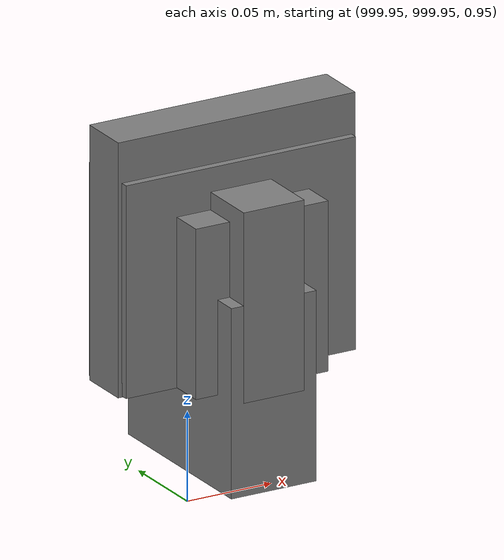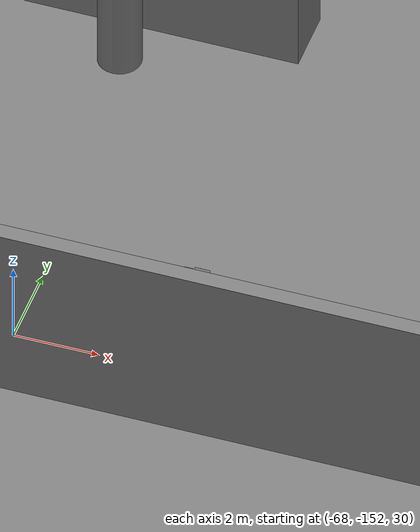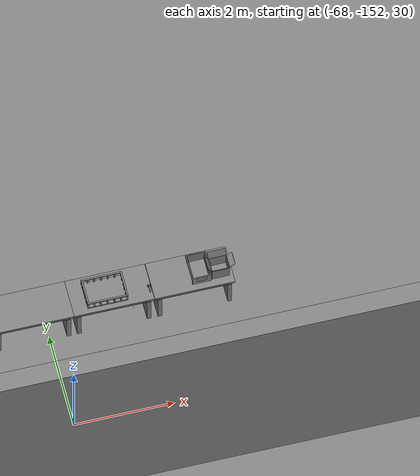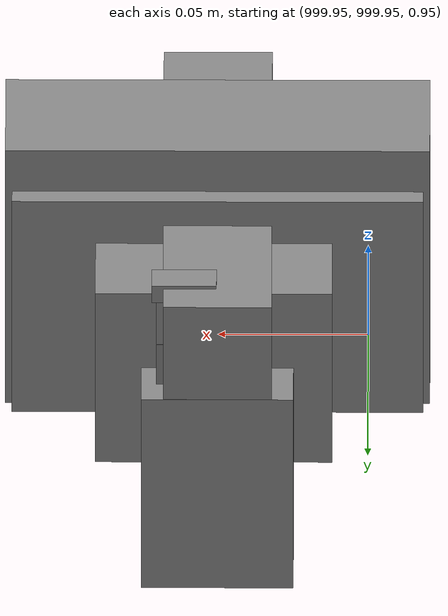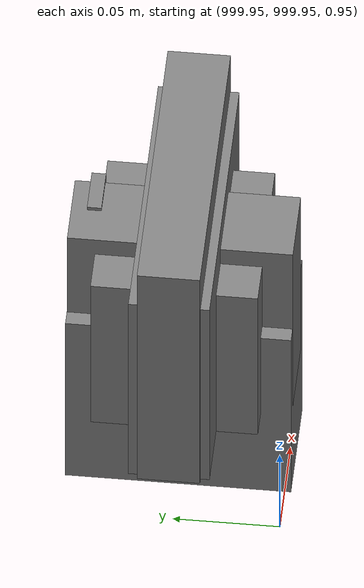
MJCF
<mujoco>
    <option gravity="0.000000000 0.000000000 -9.810000420" timestep="0.0049999999" integrator="implicitfast" density="1.225" viscosity="1.8000001e-05" noslip_iterations="10" iterations="100" sdf_iterations="50">
        <flag multiccd="disable"/>
    </option>
    <size memory="1000M"/>
    <compiler coordinate="local"/>
    <worldbody>
        <light cutoff="30" pos="0 1 1" dir="0 -1 -2"/>
        <light cutoff="30" pos="0 -1 1" dir="0 1 -2"/>
        <body pos="-64.866622925 -149.383972168 30.183746338" euler="89.999984741 89.999946594 0.000000000" name="openloong_gripper_2f85_fix_base_usda_bluebox_01">
            <geom contype="1" conaffinity="1" density="1000" type="box" material="" rgba="0.500000000 0.500000000 0.500000000 1.000000000" solimp="0.899999976 0.949999988 0.001000000" friction="1.000000000 0.005000000 0.000100000" solref="0.020000000 1.000000000" margin="0" condim="3" group="0" pos="0.276580811 0.187225342 0.000068665" quat="0.707106948 0.000077471 0.707106352 0.000077486" size="0.100000001 0.057999998 0.010000000" name="openloong_gripper_2f85_fix_base_usda_geom_27F7FE5B_28D8_449C_860D_8D4A32E26184"/>
            <geom contype="1" conaffinity="1" density="1000" type="box" material="" rgba="0.500000000 0.500000000 0.500000000 1.000000000" solimp="0.899999976 0.949999988 0.001000000" friction="1.000000000 0.005000000 0.000100000" solref="0.020000000 1.000000000" margin="0" condim="3" group="0" pos="0.000000000 0.002883911 0.000000000" quat="0.999999881 0.000000000 0.000000000 0.000000000" size="0.254000008 0.003000000 0.172000006" name="openloong_gripper_2f85_fix_base_usda_geom_86537283_C043_4C7B_8D59_D451C8E90462"/>
            <geom contype="1" conaffinity="1" density="1000" type="box" material="" rgba="0.500000000 0.500000000 0.500000000 1.000000000" solimp="0.899999976 0.949999988 0.001000000" friction="1.000000000 0.005000000 0.000100000" solref="0.020000000 1.000000000" margin="0" condim="3" group="0" pos="0.000000000 0.124874115 0.173484802" quat="0.999796331 0.020176515 -0.000000015 0.000000030" size="0.259999990 0.119999997 0.007000000" name="openloong_gripper_2f85_fix_base_usda_geom_22BF250C_DE0F_430D_8F58_79E580FAC8D5"/>
            <geom contype="1" conaffinity="1" density="1000" type="box" material="" rgba="0.500000000 0.500000000 0.500000000 1.000000000" solimp="0.899999976 0.949999988 0.001000000" friction="1.000000000 0.005000000 0.000100000" solref="0.020000000 1.000000000" margin="0" condim="3" group="0" pos="0.000000000 0.124874115 -0.173469543" quat="0.999796331 -0.020176545 -0.000000015 0.000000000" size="0.259999990 0.119999997 0.007000000" name="openloong_gripper_2f85_fix_base_usda_geom_BC030662_9DAF_49B1_B20B_DA759204FE84"/>
            <geom contype="1" conaffinity="1" density="1000" type="box" material="" rgba="0.500000000 0.500000000 0.500000000 1.000000000" solimp="0.899999976 0.949999988 0.001000000" friction="1.000000000 0.005000000 0.000100000" solref="0.020000000 1.000000000" margin="0" condim="3" group="0" pos="0.000000000 0.214008331 0.188980103" quat="0.999912977 0.013176724 0.000000015 0.000000000" size="0.259999990 0.029999999 0.012500000" name="openloong_gripper_2f85_fix_base_usda_geom_0D2F861F_5C70_4AB7_9BD6_917850D1A5C0"/>
            <geom contype="1" conaffinity="1" density="1000" type="box" material="" rgba="0.500000000 0.500000000 0.500000000 1.000000000" solimp="0.899999976 0.949999988 0.001000000" friction="1.000000000 0.005000000 0.000100000" solref="0.020000000 1.000000000" margin="0" condim="3" group="0" pos="-0.258361816 0.125289917 0.001876831" quat="0.702796936 -0.020792112 0.710783124 0.020769298" size="0.189999998 0.119999997 0.009000000" name="openloong_gripper_2f85_fix_base_usda_geom_D9D777ED_ABC2_4EAB_B4C6_1EF5DA09B9B2"/>
            <geom contype="1" conaffinity="1" density="1000" type="box" material="" rgba="0.500000000 0.500000000 0.500000000 1.000000000" solimp="0.899999976 0.949999988 0.001000000" friction="1.000000000 0.005000000 0.000100000" solref="0.020000000 1.000000000" margin="0" condim="3" group="0" pos="0.000000000 0.214008331 -0.188980103" quat="0.999912977 -0.013176769 0.000000030 0.000000015" size="0.259999990 0.029999999 0.012500000" name="openloong_gripper_2f85_fix_base_usda_geom_8EF07B3E_72A5_4229_987E_E0DF166FF4CF"/>
            <geom contype="1" conaffinity="1" density="1000" type="box" material="" rgba="0.500000000 0.500000000 0.500000000 1.000000000" solimp="0.899999976 0.949999988 0.001000000" friction="1.000000000 0.005000000 0.000100000" solref="0.020000000 1.000000000" margin="0" condim="3" group="0" pos="-0.276611328 0.187225342 0.000068665" quat="0.707106650 0.000077441 0.707106709 0.000077456" size="0.100000001 0.057999998 0.010000000" name="openloong_gripper_2f85_fix_base_usda_geom_7C005F2D_4D30_47CD_9F53_95A0C63AF59A"/>
            <geom contype="1" conaffinity="1" density="1000" type="box" material="" rgba="0.500000000 0.500000000 0.500000000 1.000000000" solimp="0.899999976 0.949999988 0.001000000" friction="1.000000000 0.005000000 0.000100000" solref="0.020000000 1.000000000" margin="0" condim="3" group="0" pos="0.258331299 0.125289917 0.001876831" quat="0.702851415 0.018856421 0.710823774 -0.019329369" size="0.189999998 0.119999997 0.009000000" name="openloong_gripper_2f85_fix_base_usda_geom_D8A39403_FCD9_4D57_B44A_4BF2F13F7BF2"/>
            <freejoint name="openloong_gripper_2f85_fix_base_usda_bluebox_01_joint"/>
            <site size="0.005000000 0.005000000 0.005000000" rgba="0.500000000 0.500000000 0.500000000 1.000000000" pos="0.000000000 0.000000000 0.000000000" quat="0.999961913 0.008726534 0.000000000 0.000000000" group="0" type="sphere" name="openloong_gripper_2f85_fix_base_usda_bluebox_01site"/>
        </body>
        <body pos="-64.496299744 -149.491867065 30.235729218" euler="0.000000000 0.000000000 89.999946594" name="openloong_gripper_2f85_fix_base_usda_cardboardbox_01">
            <geom contype="1" conaffinity="1" density="1000" type="box" material="" rgba="0.500000000 0.500000000 0.500000000 1.000000000" solimp="0.899999976 0.949999988 0.001000000" friction="1.000000000 0.005000000 0.000100000" solref="0.020000000 1.000000000" margin="0" condim="3" group="0" pos="-0.003166199 -0.004086494 0.005052090" quat="1.000000000 0.000000000 0.000000000 0.000000000" size="0.142499998 0.177500010 0.005000000" name="openloong_gripper_2f85_fix_base_usda_geom_3787E039_9E9E_48F5_8A56_6019245D357A"/>
            <geom contype="1" conaffinity="1" density="1000" type="box" material="" rgba="0.500000000 0.500000000 0.500000000 1.000000000" solimp="0.899999976 0.949999988 0.001000000" friction="1.000000000 0.005000000 0.000100000" solref="0.020000000 1.000000000" margin="0" condim="3" group="0" pos="-0.003166199 0.170316696 0.150570869" quat="1.000000000 0.000000000 0.000000000 0.000000000" size="0.142499998 0.005000000 0.149999991" name="openloong_gripper_2f85_fix_base_usda_geom_F93D37C0_0A9F_4191_8A3B_2497EEF83D41"/>
            <geom contype="1" conaffinity="1" density="1000" type="box" material="" rgba="0.500000000 0.500000000 0.500000000 1.000000000" solimp="0.899999976 0.949999988 0.001000000" friction="1.000000000 0.005000000 0.000100000" solref="0.020000000 1.000000000" margin="0" condim="3" group="0" pos="-0.147399902 -0.005307198 0.150570869" quat="1.000000000 0.000000000 0.000000000 0.000000000" size="0.005000000 0.177500010 0.149999991" name="openloong_gripper_2f85_fix_base_usda_geom_066B0CDC_6C26_46E7_9074_EAF3E9024FB0"/>
            <geom contype="1" conaffinity="1" density="1000" type="box" material="" rgba="0.500000000 0.500000000 0.500000000 1.000000000" solimp="0.899999976 0.949999988 0.001000000" friction="1.000000000 0.005000000 0.000100000" solref="0.020000000 1.000000000" margin="0" condim="3" group="0" pos="0.140275955 -0.005307198 0.150570869" quat="1.000000000 0.000000000 0.000000000 0.000000000" size="0.005000000 0.177500010 0.149999991" name="openloong_gripper_2f85_fix_base_usda_geom_AC1F578F_58C1_4F26_B507_862FA1C2CC1B"/>
            <geom contype="1" conaffinity="1" density="1000" type="box" material="" rgba="0.500000000 0.500000000 0.500000000 1.000000000" solimp="0.899999976 0.949999988 0.001000000" friction="1.000000000 0.005000000 0.000100000" solref="0.020000000 1.000000000" margin="0" condim="3" group="0" pos="-0.003166199 -0.181550980 0.150570869" quat="1.000000000 0.000000000 0.000000000 0.000000000" size="0.142499998 0.005000000 0.149999991" name="openloong_gripper_2f85_fix_base_usda_geom_3CBD1BF2_BEFF_4C92_BA74_27EC692683C7"/>
            <freejoint name="openloong_gripper_2f85_fix_base_usda_cardboardbox_01_joint"/>
            <site size="0.005000000 0.005000000 0.005000000" rgba="0.500000000 0.500000000 0.500000000 1.000000000" pos="0.000000000 0.000000000 0.000000000" quat="0.999961913 0.008726535 0.000000000 0.000000000" group="0" type="sphere" name="openloong_gripper_2f85_fix_base_usda_site_6000F812_14BA_4891_9F3F_56811E488AA1"/>
            <body pos="0.139160156 -0.004048347 0.301930904" euler="-179.999954224 49.383502960 179.999954224" name="openloong_gripper_2f85_fix_base_usda_A1_006">
                <geom contype="1" conaffinity="1" density="1000" type="box" material="" rgba="0.500000000 0.500000000 0.500000000 1.000000000" solimp="0.899999976 0.949999988 0.001000000" friction="1.000000000 0.005000000 0.000100000" solref="0.020000000 1.000000000" margin="0" condim="3" group="0" pos="-0.071587563 0.000009537 0.001745224" quat="0.999999881 0.000000000 0.000000000 0.000000000" size="0.071249999 0.179999992 0.002500000" name="openloong_gripper_2f85_fix_base_usda_geom_66BC1B6A_31B9_4975_88C9_CF54FB0C0379"/>
                <joint armature="0" stiffness="0.07" damping="0.0099999998" axis="0.000000 1.000000 0.000000" type="hinge" name="openloong_gripper_2f85_fix_base_usda_A1_006"/>
            </body>
            <body pos="-0.145902634 -0.004086494 0.301938057" euler="-180.000000000 -60.000011444 -180.000000000" name="openloong_gripper_2f85_fix_base_usda_A2_006">
                <geom contype="1" conaffinity="1" density="1000" type="box" material="" rgba="0.500000000 0.500000000 0.500000000 1.000000000" solimp="0.899999976 0.949999988 0.001000000" friction="1.000000000 0.005000000 0.000100000" solref="0.020000000 1.000000000" margin="0" condim="3" group="0" pos="0.071268082 0.000009537 0.002717972" quat="0.000002921 0.000000000 -0.000000030 0.999999881" size="0.071249999 0.179999992 0.002500000" name="openloong_gripper_2f85_fix_base_usda_geom_43F27F92_F807_4C0D_8FC8_9EFD3E4B47D6"/>
                <joint armature="0" stiffness="0.07" damping="0.0099999998" axis="0.000000 1.000000 0.000000" type="hinge" name="openloong_gripper_2f85_fix_base_usda_A2_006"/>
            </body>
            <body pos="-0.003385544 0.175991058 0.301930904" euler="-125.858116150 -0.000004561 0.000002331" name="openloong_gripper_2f85_fix_base_usda_B2_006">
                <geom contype="1" conaffinity="1" density="1000" type="box" material="" rgba="0.500000000 0.500000000 0.500000000 1.000000000" solimp="0.899999976 0.949999988 0.001000000" friction="1.000000000 0.005000000 0.000100000" solref="0.020000000 1.000000000" margin="0" condim="3" group="0" pos="0.000009537 -0.070939064 -0.002470016" quat="0.999614120 0.027776197 -0.000000015 0.000000030" size="0.137500003 0.064999998 0.005000000" name="openloong_gripper_2f85_fix_base_usda_geom_13A41FCC_B0F1_4EC6_B511_2783CA6D3DC4"/>
                <joint armature="0" stiffness="0.07" damping="0.0099999998" axis="1.000000 0.000000 0.000000" type="hinge" name="openloong_gripper_2f85_fix_base_usda_B2_006"/>
            </body>
            <body pos="-0.003385544 -0.184140205 0.301938057" euler="147.805557251 0.000000000 0.000000000" name="openloong_gripper_2f85_fix_base_usda_B1_006">
                <geom contype="1" conaffinity="1" density="1000" type="box" material="" rgba="0.500000000 0.500000000 0.500000000 1.000000000" solimp="0.899999976 0.949999988 0.001000000" friction="1.000000000 0.005000000 0.000100000" solref="0.020000000 1.000000000" margin="0" condim="3" group="0" pos="-0.000028610 0.070202351 -0.002703667" quat="0.999614179 -0.027776167 0.000000000 0.000000000" size="0.137500003 0.064999998 0.005000000" name="openloong_gripper_2f85_fix_base_usda_geom_78A16A7E_0BD5_4577_88BF_C3FAB93C29C8"/>
                <joint armature="0" stiffness="0.07" damping="0.0099999998" axis="1.000000 0.000000 0.000000" type="hinge" name="openloong_gripper_2f85_fix_base_usda_B1_006"/>
            </body>
        </body>
        <body pos="-65.882858276 -149.481979370 30.229999542" euler="-64.487716675 0.000000000 0.000000000" name="openloong_gripper_2f85_fix_base_usda_Barcode">
            <geom contype="1" conaffinity="1" density="1000" type="box" material="" rgba="0.500000000 0.500000000 0.500000000 1.000000000" solimp="0.899999976 0.949999988 0.001000000" friction="1.000000000 0.005000000 0.000100000" solref="0.020000000 1.000000000" margin="0" condim="3" group="0" pos="0.000000000 0.013038635 0.001419067" quat="0.000000000 0.000000000 0.000000000 1.000000119" size="0.034000002 0.010000000 0.017999999" name="openloong_gripper_2f85_fix_base_usda_geom_6AD1666A_A1DD_4547_BF9E_46E2F0CB65BA"/>
            <geom contype="1" conaffinity="1" density="1000" type="box" material="" rgba="0.500000000 0.500000000 0.500000000 1.000000000" solimp="0.899999976 0.949999988 0.001000000" friction="1.000000000 0.005000000 0.000100000" solref="0.020000000 1.000000000" margin="0" condim="3" group="0" pos="0.000000000 -0.035301208 -0.007095337" quat="0.000000000 0.000000000 -0.043619365 0.999048233" size="0.028999999 0.010000000 0.020000000" name="openloong_gripper_2f85_fix_base_usda_geom_F09326AE_BFBB_4DEE_A999_2DB9238913CC"/>
            <geom contype="1" conaffinity="1" density="1000" type="box" material="" rgba="0.500000000 0.500000000 0.500000000 1.000000000" solimp="0.899999976 0.949999988 0.001000000" friction="1.000000000 0.005000000 0.000100000" solref="0.020000000 1.000000000" margin="0" condim="3" group="0" pos="0.000000000 -0.043411255 -0.011749268" quat="0.922262907 0.386563420 0.000000000 0.000000000" size="0.026000001 0.010000000 0.020000000" name="openloong_gripper_2f85_fix_base_usda_geom_DD9FE27C_9A4E_4B13_9FEE_9CE24536ED53"/>
            <geom contype="1" conaffinity="1" density="1000" type="box" material="" rgba="0.500000000 0.500000000 0.500000000 1.000000000" solimp="0.899999976 0.949999988 0.001000000" friction="1.000000000 0.005000000 0.000100000" solref="0.020000000 1.000000000" margin="0" condim="3" group="0" pos="0.000000000 -0.016967773 -0.031860352" quat="0.000000000 0.000000000 0.000000000 1.000000119" size="0.008000000 0.010000000 0.013000000" name="openloong_gripper_2f85_fix_base_usda_geom_D5A54714_C702_423C_A44B_A8C870955B0F"/>
            <geom contype="1" conaffinity="1" density="1000" type="box" material="" rgba="0.500000000 0.500000000 0.500000000 1.000000000" solimp="0.899999976 0.949999988 0.001000000" friction="1.000000000 0.005000000 0.000100000" solref="0.020000000 1.000000000" margin="0" condim="3" group="0" pos="0.000000000 -0.001869202 0.000312805" quat="0.953716993 0.300705761 0.000000000 0.000000000" size="0.032000002 0.010000000 0.018999999" name="openloong_gripper_2f85_fix_base_usda_geom_9536DFE4_06D1_4A11_B2EF_22B57ACB2426"/>
            <geom contype="1" conaffinity="1" density="1000" type="box" material="" rgba="0.500000000 0.500000000 0.500000000 1.000000000" solimp="0.899999976 0.949999988 0.001000000" friction="1.000000000 0.005000000 0.000100000" solref="0.020000000 1.000000000" margin="0" condim="3" group="0" pos="0.000000000 -0.019531250 -0.003173828" quat="0.953716993 0.300705761 0.000000000 0.000000000" size="0.030999999 0.010000000 0.020000000" name="openloong_gripper_2f85_fix_base_usda_geom_5874994F_5E86_430C_8C12_F89D8DB97658"/>
            <geom contype="1" conaffinity="1" density="1000" type="box" material="" rgba="0.500000000 0.500000000 0.500000000 1.000000000" solimp="0.899999976 0.949999988 0.001000000" friction="1.000000000 0.005000000 0.000100000" solref="0.020000000 1.000000000" margin="0" condim="3" group="0" pos="0.000000000 -0.035301208 -0.007095337" quat="0.953716993 0.300705761 0.000000000 0.000000000" size="0.028999999 0.010000000 0.020000000" name="openloong_gripper_2f85_fix_base_usda_geom_6A49E068_D826_4B9A_AB15_AE0AF9487E0E"/>
            <geom contype="1" conaffinity="1" density="1000" type="box" material="" rgba="0.500000000 0.500000000 0.500000000 1.000000000" solimp="0.899999976 0.949999988 0.001000000" friction="1.000000000 0.005000000 0.000100000" solref="0.020000000 1.000000000" margin="0" condim="3" group="0" pos="0.000000000 -0.042617798 -0.071121216" quat="0.000000000 0.000000000 0.000000000 1.000000119" size="0.013000000 0.021000000 0.059999999" name="openloong_gripper_2f85_fix_base_usda_geom_1BDFA439_FDBB_4017_82E4_B9A27C9BA8B3"/>
            <freejoint name="openloong_gripper_2f85_fix_base_usda_Barcode_joint"/>
            <site size="0.005000000 0.005000000 0.005000000" rgba="0.500000000 0.500000000 0.500000000 1.000000000" pos="0.000000000 0.000000000 0.000000000" quat="1.000000000 0.000000000 0.000000000 0.000000000" group="0" type="sphere" name="openloong_gripper_2f85_fix_base_usda_Barcode_site"/>
        </body>
        <body pos="-66.745018005 -149.392349243 30.184000015" euler="0.000000000 0.000000000 89.999946594" name="[22332718441649]_Basket_01">
            <geom contype="1" conaffinity="1" density="1000" type="box" material="" rgba="0.500000000 0.500000000 0.500000000 1.000000000" solimp="0.899999976 0.949999988 0.001000000" friction="1.000000000 0.005000000 0.000100000" solref="0.020000000 1.000000000" margin="0" condim="3" group="0" pos="-0.052425385 0.389207840 0.089787483" quat="0.707107008 0.000000000 0.000000000 0.707106411" size="0.014249999 0.014249999 0.059999999" name="[22332718441649]_geom_134295E4_322A_458F_B99B_21F09611F7A2"/>
            <geom contype="1" conaffinity="1" density="1000" type="box" material="" rgba="0.500000000 0.500000000 0.500000000 1.000000000" solimp="0.899999976 0.949999988 0.001000000" friction="1.000000000 0.005000000 0.000100000" solref="0.020000000 1.000000000" margin="0" condim="3" group="0" pos="0.264015198 -0.133043289 0.089787483" quat="0.707107008 0.000000000 0.000000000 0.707106411" size="0.014249999 0.014249999 0.059999999" name="[22332718441649]_geom_80577372_CD43_4CA1_A1D4_A01018DE7F7F"/>
            <geom contype="1" conaffinity="1" density="1000" type="box" material="" rgba="0.500000000 0.500000000 0.500000000 1.000000000" solimp="0.899999976 0.949999988 0.001000000" friction="1.000000000 0.005000000 0.000100000" solref="0.020000000 1.000000000" margin="0" condim="3" group="0" pos="-0.264015198 -0.265548706 0.089793205" quat="0.707107008 0.000000000 0.000000000 0.707106411" size="0.014249999 0.014249999 0.059999999" name="[22332718441649]_geom_92EA3DE0_5D9A_4569_8E00_F392A651B6C1"/>
            <geom contype="1" conaffinity="1" density="1000" type="box" material="" rgba="0.500000000 0.500000000 0.500000000 1.000000000" solimp="0.899999976 0.949999988 0.001000000" friction="1.000000000 0.005000000 0.000100000" solref="0.020000000 1.000000000" margin="0" condim="3" group="0" pos="-0.160263062 -0.389322281 0.089793205" quat="0.707107008 0.000000000 0.000000000 0.707106411" size="0.014249999 0.014249999 0.059999999" name="[22332718441649]_geom_A2B164A1_1631_4E52_B964_41AF732FB516"/>
            <geom contype="1" conaffinity="1" density="1000" type="box" material="" rgba="0.500000000 0.500000000 0.500000000 1.000000000" solimp="0.899999976 0.949999988 0.001000000" friction="1.000000000 0.005000000 0.000100000" solref="0.020000000 1.000000000" margin="0" condim="3" group="0" pos="0.162265778 -0.389322281 0.089787483" quat="0.707107008 0.000000000 0.000000000 0.707106411" size="0.014249999 0.014249999 0.059999999" name="[22332718441649]_geom_55E8A328_0872_4A86_B32A_229C916B6587"/>
            <geom contype="1" conaffinity="1" density="1000" type="box" material="" rgba="0.500000000 0.500000000 0.500000000 1.000000000" solimp="0.899999976 0.949999988 0.001000000" friction="1.000000000 0.005000000 0.000100000" solref="0.020000000 1.000000000" margin="0" condim="3" group="0" pos="0.264015198 0.389207840 0.089787483" quat="0.707107008 0.000000000 0.000000000 0.707106411" size="0.014249999 0.014249999 0.059999999" name="[22332718441649]_geom_B726EC38_288F_4BA2_A091_77EBBE90BA4A"/>
            <geom contype="1" conaffinity="1" density="1000" type="box" material="" rgba="0.500000000 0.500000000 0.500000000 1.000000000" solimp="0.899999976 0.949999988 0.001000000" friction="1.000000000 0.005000000 0.000100000" solref="0.020000000 1.000000000" margin="0" condim="3" group="0" pos="-0.264015198 -0.133043289 0.089793205" quat="0.707107008 0.000000000 0.000000000 0.707106411" size="0.014249999 0.014249999 0.059999999" name="[22332718441649]_geom_751E17C0_A2C7_4893_9F9D_1758D224FA54"/>
            <geom contype="1" conaffinity="1" density="1000" type="box" material="" rgba="0.500000000 0.500000000 0.500000000 1.000000000" solimp="0.899999976 0.949999988 0.001000000" friction="1.000000000 0.005000000 0.000100000" solref="0.020000000 1.000000000" margin="0" condim="3" group="0" pos="-0.264026642 0.269256592 0.089793205" quat="0.707107008 0.000000000 0.000000000 0.707106411" size="0.014249999 0.014249999 0.059999999" name="[22332718441649]_geom_A3FDD257_139C_47E4_815B_418E3660566C"/>
            <geom contype="1" conaffinity="1" density="1000" type="box" material="" rgba="0.500000000 0.500000000 0.500000000 1.000000000" solimp="0.899999976 0.949999988 0.001000000" friction="1.000000000 0.005000000 0.000100000" solref="0.020000000 1.000000000" margin="0" condim="3" group="0" pos="0.054462433 0.389207840 0.089787483" quat="0.707107008 0.000000000 0.000000000 0.707106411" size="0.014249999 0.014249999 0.059999999" name="[22332718441649]_geom_1ADBA82B_2B0D_4D81_8810_C3B129A14391"/>
            <geom contype="1" conaffinity="1" density="1000" type="box" material="" rgba="0.500000000 0.500000000 0.500000000 1.000000000" solimp="0.899999976 0.949999988 0.001000000" friction="1.000000000 0.005000000 0.000100000" solref="0.020000000 1.000000000" margin="0" condim="3" group="0" pos="0.054462433 -0.389322281 0.089787483" quat="0.707107008 0.000000000 0.000000000 0.707106411" size="0.014249999 0.014249999 0.059999999" name="[22332718441649]_geom_BF25A5BC_BA13_4397_97CA_F6498DD22CE8"/>
            <geom contype="1" conaffinity="1" density="1000" type="box" material="" rgba="0.500000000 0.500000000 0.500000000 1.000000000" solimp="0.899999976 0.949999988 0.001000000" friction="1.000000000 0.005000000 0.000100000" solref="0.020000000 1.000000000" margin="0" condim="3" group="0" pos="0.264015198 0.269256592 0.089793205" quat="0.707107008 0.000000000 0.000000000 0.707106411" size="0.014249999 0.014249999 0.059999999" name="[22332718441649]_geom_A5B512F8_B0FA_498D_A74D_A5F0F2CBC309"/>
            <geom contype="1" conaffinity="1" density="1000" type="box" material="" rgba="0.500000000 0.500000000 0.500000000 1.000000000" solimp="0.899999976 0.949999988 0.001000000" friction="1.000000000 0.005000000 0.000100000" solref="0.020000000 1.000000000" margin="0" condim="3" group="0" pos="0.264015198 -0.389322281 0.089787483" quat="0.707107008 0.000000000 0.000000000 0.707106411" size="0.014249999 0.014249999 0.059999999" name="[22332718441649]_geom_A703AE5A_EA04_4323_B123_A19E4BFC10ED"/>
            <geom contype="1" conaffinity="1" density="1000" type="box" material="" rgba="0.500000000 0.500000000 0.500000000 1.000000000" solimp="0.899999976 0.949999988 0.001000000" friction="1.000000000 0.005000000 0.000100000" solref="0.020000000 1.000000000" margin="0" condim="3" group="0" pos="0.000000000 0.000000000 0.015998840" quat="0.707107008 0.000000000 0.000000000 0.707106411" size="0.403499991 0.279000014 0.015750000" name="[22332718441649]_geom_D729D0CF_EF1C_457A_A6D7_AAA0A5524413"/>
            <geom contype="1" conaffinity="1" density="1000" type="box" material="" rgba="0.500000000 0.500000000 0.500000000 1.000000000" solimp="0.899999976 0.949999988 0.001000000" friction="1.000000000 0.005000000 0.000100000" solref="0.020000000 1.000000000" margin="0" condim="3" group="0" pos="0.000000000 -0.389476776 0.163619041" quat="0.707107008 0.000000000 0.000000000 0.707106411" size="0.015000000 0.277500004 0.015750000" name="[22332718441649]_geom_B5BEABD0_55F1_4480_9114_8B9EDC7D78FA"/>
            <geom contype="1" conaffinity="1" density="1000" type="box" material="" rgba="0.500000000 0.500000000 0.500000000 1.000000000" solimp="0.899999976 0.949999988 0.001000000" friction="1.000000000 0.005000000 0.000100000" solref="0.020000000 1.000000000" margin="0" condim="3" group="0" pos="0.162265778 0.389207840 0.089787483" quat="0.707107008 0.000000000 0.000000000 0.707106411" size="0.014249999 0.014249999 0.059999999" name="[22332718441649]_geom_4C14F1F1_5834_47B5_8414_BB40FBB28C4C"/>
            <geom contype="1" conaffinity="1" density="1000" type="box" material="" rgba="0.500000000 0.500000000 0.500000000 1.000000000" solimp="0.899999976 0.949999988 0.001000000" friction="1.000000000 0.005000000 0.000100000" solref="0.020000000 1.000000000" margin="0" condim="3" group="0" pos="0.000000000 0.389471054 0.163619041" quat="0.707107008 0.000000000 0.000000000 0.707106411" size="0.015000000 0.277500004 0.015750000" name="[22332718441649]_geom_0667ADE0_2C79_4587_993B_6755630EE84C"/>
            <geom contype="1" conaffinity="1" density="1000" type="box" material="" rgba="0.500000000 0.500000000 0.500000000 1.000000000" solimp="0.899999976 0.949999988 0.001000000" friction="1.000000000 0.005000000 0.000100000" solref="0.020000000 1.000000000" margin="0" condim="3" group="0" pos="-0.263511658 0.000000000 0.163619041" quat="0.707107008 0.000000000 0.000000000 0.707106411" size="0.403499991 0.015000000 0.015750000" name="[22332718441649]_geom_8EF0F948_11CF_47D8_A91F_1450EF897256"/>
            <geom contype="1" conaffinity="1" density="1000" type="box" material="" rgba="0.500000000 0.500000000 0.500000000 1.000000000" solimp="0.899999976 0.949999988 0.001000000" friction="1.000000000 0.005000000 0.000100000" solref="0.020000000 1.000000000" margin="0" condim="3" group="0" pos="-0.264015198 0.141334534 0.089793205" quat="0.707107008 0.000000000 0.000000000 0.707106411" size="0.014249999 0.014249999 0.059999999" name="[22332718441649]_geom_175D17CC_4EBC_4A9D_B0E0_2E4A3FEF26A1"/>
            <geom contype="1" conaffinity="1" density="1000" type="box" material="" rgba="0.500000000 0.500000000 0.500000000 1.000000000" solimp="0.899999976 0.949999988 0.001000000" friction="1.000000000 0.005000000 0.000100000" solref="0.020000000 1.000000000" margin="0" condim="3" group="0" pos="0.264015198 -0.265548706 0.089787483" quat="0.707107008 0.000000000 0.000000000 0.707106411" size="0.014249999 0.014249999 0.059999999" name="[22332718441649]_geom_AE4ED6C6_5D72_4694_AF94_656AB2917573"/>
            <geom contype="1" conaffinity="1" density="1000" type="box" material="" rgba="0.500000000 0.500000000 0.500000000 1.000000000" solimp="0.899999976 0.949999988 0.001000000" friction="1.000000000 0.005000000 0.000100000" solref="0.020000000 1.000000000" margin="0" condim="3" group="0" pos="-0.160263062 0.389207840 0.089787483" quat="0.707107008 0.000000000 0.000000000 0.707106411" size="0.014249999 0.014249999 0.059999999" name="[22332718441649]_geom_CA43C10D_5847_4CA5_AC73_86BC188366E2"/>
            <geom contype="1" conaffinity="1" density="1000" type="box" material="" rgba="0.500000000 0.500000000 0.500000000 1.000000000" solimp="0.899999976 0.949999988 0.001000000" friction="1.000000000 0.005000000 0.000100000" solref="0.020000000 1.000000000" margin="0" condim="3" group="0" pos="-0.052425385 -0.389322281 0.089787483" quat="0.707107008 0.000000000 0.000000000 0.707106411" size="0.014249999 0.014249999 0.059999999" name="[22332718441649]_geom_D5FFCC08_FCCA_4DA3_A2F4_76D31CF360FF"/>
            <geom contype="1" conaffinity="1" density="1000" type="box" material="" rgba="0.500000000 0.500000000 0.500000000 1.000000000" solimp="0.899999976 0.949999988 0.001000000" friction="1.000000000 0.005000000 0.000100000" solref="0.020000000 1.000000000" margin="0" condim="3" group="0" pos="-0.264026642 -0.389322281 0.089793205" quat="0.707107008 0.000000000 0.000000000 0.707106411" size="0.014249999 0.014249999 0.059999999" name="[22332718441649]_geom_372E4E99_FDAD_426D_8103_22C384EDF05F"/>
            <geom contype="1" conaffinity="1" density="1000" type="box" material="" rgba="0.500000000 0.500000000 0.500000000 1.000000000" solimp="0.899999976 0.949999988 0.001000000" friction="1.000000000 0.005000000 0.000100000" solref="0.020000000 1.000000000" margin="0" condim="3" group="0" pos="0.264015198 0.141334534 0.089787483" quat="0.707107008 0.000000000 0.000000000 0.707106411" size="0.014249999 0.014249999 0.059999999" name="[22332718441649]_geom_816DABB6_2959_4A7C_8EBB_106A61F25CBA"/>
            <geom contype="1" conaffinity="1" density="1000" type="box" material="" rgba="0.500000000 0.500000000 0.500000000 1.000000000" solimp="0.899999976 0.949999988 0.001000000" friction="1.000000000 0.005000000 0.000100000" solref="0.020000000 1.000000000" margin="0" condim="3" group="0" pos="-0.264015198 0.389207840 0.089793205" quat="0.707107008 0.000000000 0.000000000 0.707106411" size="0.014249999 0.014249999 0.059999999" name="[22332718441649]_geom_4845DBA6_CFE2_46EE_8470_57704476D3AD"/>
            <geom contype="1" conaffinity="1" density="1000" type="box" material="" rgba="0.500000000 0.500000000 0.500000000 1.000000000" solimp="0.899999976 0.949999988 0.001000000" friction="1.000000000 0.005000000 0.000100000" solref="0.020000000 1.000000000" margin="0" condim="3" group="0" pos="0.264015198 0.004480362 0.089787483" quat="0.707107008 0.000000000 0.000000000 0.707106411" size="0.014249999 0.014249999 0.059999999" name="[22332718441649]_geom_04574E7E_926E_4AC3_A0EB_46E46EA2F6A9"/>
            <geom contype="1" conaffinity="1" density="1000" type="box" material="" rgba="0.500000000 0.500000000 0.500000000 1.000000000" solimp="0.899999976 0.949999988 0.001000000" friction="1.000000000 0.005000000 0.000100000" solref="0.020000000 1.000000000" margin="0" condim="3" group="0" pos="0.263694763 -0.000011444 0.163619041" quat="0.707107008 0.000000000 0.000000000 0.707106411" size="0.403499991 0.015000000 0.015750000" name="[22332718441649]_geom_E463D5AD_E611_4B2A_A68D_D625DB603973"/>
            <geom contype="1" conaffinity="1" density="1000" type="box" material="" rgba="0.500000000 0.500000000 0.500000000 1.000000000" solimp="0.899999976 0.949999988 0.001000000" friction="1.000000000 0.005000000 0.000100000" solref="0.020000000 1.000000000" margin="0" condim="3" group="0" pos="-0.264015198 0.004480362 0.089793205" quat="0.707107008 0.000000000 0.000000000 0.707106411" size="0.014249999 0.014249999 0.059999999" name="[22332718441649]_geom_4CEA0D39_0657_454E_8E3B_2BC1D44906B7"/>
            <freejoint name="[22332718441649]_joint_E884F241_C5F4_4B44_8CA0_964EDF37D93C"/>
        </body>
        <body pos="0.000000000 0.000000000 0.000000000" euler="0.000000000 0.000000000 0.000000000" name="Static Objects_Static Objects">
            <geom contype="1" conaffinity="1" density="1000" type="box" material="" rgba="0.500000000 0.500000000 0.500000000 1.000000000" solimp="0.899999976 0.949999988 0.001000000" friction="1.000000000 0.005000000 0.000100000" solref="0.020000000 1.000000000" margin="0" condim="3" group="0" pos="-67.544113159 -149.365814209 29.727830887" quat="0.500000417 0.499999970 0.499999553 0.499999970" size="0.381000012 0.319999993 0.041000001" name="Static Objects_geom_9D71671E_04A2_4FB1_927E_D408A98CB420"/>
            <geom contype="1" conaffinity="1" density="1000" type="box" material="" rgba="0.500000000 0.500000000 0.500000000 1.000000000" solimp="0.899999976 0.949999988 0.001000000" friction="1.000000000 0.005000000 0.000100000" solref="0.020000000 1.000000000" margin="0" condim="3" group="0" pos="-68.239501953 -149.365814209 30.086868286" quat="0.500000417 0.499999970 0.499999553 0.499999970" size="0.370999992 0.039500002 0.745000005" name="Static Objects_geom_E4F50BE4_655D_4CD3_A7E8_9A5E20C5675D"/>
            <geom contype="1" conaffinity="1" density="1000" type="box" material="" rgba="0.500000000 0.500000000 0.500000000 1.000000000" solimp="0.899999976 0.949999988 0.001000000" friction="1.000000000 0.005000000 0.000100000" solref="0.020000000 1.000000000" margin="0" condim="3" group="0" pos="-68.239501953 -149.365814209 30.147235870" quat="0.500000417 0.499999970 0.499999553 0.499999970" size="0.400000006 0.022000000 0.800000012" name="Static Objects_geom_9606FB82_5449_492F_851D_B48F869A2405"/>
            <geom contype="1" conaffinity="1" density="1000" type="box" material="" rgba="0.500000000 0.500000000 0.500000000 1.000000000" solimp="0.899999976 0.949999988 0.001000000" friction="1.000000000 0.005000000 0.000100000" solref="0.020000000 1.000000000" margin="0" condim="3" group="0" pos="-68.934890747 -149.365814209 29.727830887" quat="0.500000417 0.499999970 0.499999553 0.499999970" size="0.381000012 0.319999993 0.041000001" name="Static Objects_geom_3D656F39_4EF1_45D4_9188_10FB4FC4DC57"/>
            <geom contype="1" conaffinity="1" density="1000" type="box" material="" rgba="0.500000000 0.500000000 0.500000000 1.000000000" solimp="0.899999976 0.949999988 0.001000000" friction="1.000000000 0.005000000 0.000100000" solref="0.020000000 1.000000000" margin="0" condim="3" group="0" pos="-68.239501953 -149.365814209 29.561563492" quat="0.500000417 0.499999970 0.499999553 0.499999970" size="0.020000000 0.022000000 0.660000026" name="Static Objects_geom_A6D67EB1_2440_45B3_B6A8_903ADFFB928B"/>
            <geom contype="1" conaffinity="1" density="1000" type="box" material="" rgba="0.500000000 0.500000000 0.500000000 1.000000000" solimp="0.899999976 0.949999988 0.001000000" friction="1.000000000 0.005000000 0.000100000" solref="0.020000000 1.000000000" margin="0" condim="3" group="0" pos="-65.945671082 -149.365814209 29.727830887" quat="0.500000417 0.499999970 0.499999553 0.499999970" size="0.381000012 0.319999993 0.041000001" name="Static Objects_geom_6361F209_1B61_4635_B5A2_46D06A2D7144"/>
            <geom contype="1" conaffinity="1" density="1000" type="box" material="" rgba="0.500000000 0.500000000 0.500000000 1.000000000" solimp="0.899999976 0.949999988 0.001000000" friction="1.000000000 0.005000000 0.000100000" solref="0.020000000 1.000000000" margin="0" condim="3" group="0" pos="-66.641059875 -149.365814209 30.086868286" quat="0.500000417 0.499999970 0.499999553 0.499999970" size="0.370999992 0.039500002 0.745000005" name="Static Objects_geom_CE334560_3E6B_4635_92B8_3378417B892D"/>
            <geom contype="1" conaffinity="1" density="1000" type="box" material="" rgba="0.500000000 0.500000000 0.500000000 1.000000000" solimp="0.899999976 0.949999988 0.001000000" friction="1.000000000 0.005000000 0.000100000" solref="0.020000000 1.000000000" margin="0" condim="3" group="0" pos="-66.641059875 -149.365814209 30.147235870" quat="0.500000417 0.499999970 0.499999553 0.499999970" size="0.400000006 0.022000000 0.800000012" name="Static Objects_geom_194DC239_A5E4_468D_871E_66658DF0397E"/>
            <geom contype="1" conaffinity="1" density="1000" type="box" material="" rgba="0.500000000 0.500000000 0.500000000 1.000000000" solimp="0.899999976 0.949999988 0.001000000" friction="1.000000000 0.005000000 0.000100000" solref="0.020000000 1.000000000" margin="0" condim="3" group="0" pos="-67.336448669 -149.365814209 29.727830887" quat="0.500000417 0.499999970 0.499999553 0.499999970" size="0.381000012 0.319999993 0.041000001" name="Static Objects_geom_503AC2A9_44F5_4D55_B053_DBA5CC9064C4"/>
            <geom contype="1" conaffinity="1" density="1000" type="box" material="" rgba="0.500000000 0.500000000 0.500000000 1.000000000" solimp="0.899999976 0.949999988 0.001000000" friction="1.000000000 0.005000000 0.000100000" solref="0.020000000 1.000000000" margin="0" condim="3" group="0" pos="-66.641059875 -149.365814209 29.561563492" quat="0.500000417 0.499999970 0.499999553 0.499999970" size="0.020000000 0.022000000 0.660000026" name="Static Objects_geom_79330D6E_C288_4288_B202_984987219F03"/>
            <geom contype="1" conaffinity="1" density="1000" type="box" material="" rgba="0.500000000 0.500000000 0.500000000 1.000000000" solimp="0.899999976 0.949999988 0.001000000" friction="1.000000000 0.005000000 0.000100000" solref="0.020000000 1.000000000" margin="0" condim="3" group="0" pos="-64.338577271 -149.365814209 29.727830887" quat="0.500000417 0.499999970 0.499999553 0.499999970" size="0.381000012 0.319999993 0.041000001" name="Static Objects_geom_108F833C_CCC7_4003_BAA6_93DD57DE7DA9"/>
            <geom contype="1" conaffinity="1" density="1000" type="box" material="" rgba="0.500000000 0.500000000 0.500000000 1.000000000" solimp="0.899999976 0.949999988 0.001000000" friction="1.000000000 0.005000000 0.000100000" solref="0.020000000 1.000000000" margin="0" condim="3" group="0" pos="-65.033966064 -149.365814209 30.086868286" quat="0.500000417 0.499999970 0.499999553 0.499999970" size="0.370999992 0.039500002 0.745000005" name="Static Objects_geom_E5AD87F2_DFA3_4FEC_A9F2_890492D3E818"/>
            <geom contype="1" conaffinity="1" density="1000" type="box" material="" rgba="0.500000000 0.500000000 0.500000000 1.000000000" solimp="0.899999976 0.949999988 0.001000000" friction="1.000000000 0.005000000 0.000100000" solref="0.020000000 1.000000000" margin="0" condim="3" group="0" pos="-65.033966064 -149.365814209 30.147235870" quat="0.500000417 0.499999970 0.499999553 0.499999970" size="0.400000006 0.022000000 0.800000012" name="Static Objects_geom_62196A13_2EC5_4CDE_B8E4_97C719ED8EB9"/>
            <geom contype="1" conaffinity="1" density="1000" type="box" material="" rgba="0.500000000 0.500000000 0.500000000 1.000000000" solimp="0.899999976 0.949999988 0.001000000" friction="1.000000000 0.005000000 0.000100000" solref="0.020000000 1.000000000" margin="0" condim="3" group="0" pos="-65.729354858 -149.365814209 29.727830887" quat="0.500000417 0.499999970 0.499999553 0.499999970" size="0.381000012 0.319999993 0.041000001" name="Static Objects_geom_6E1D8B4B_5015_4131_88FC_3CBC0E18A0B5"/>
            <geom contype="1" conaffinity="1" density="1000" type="box" material="" rgba="0.500000000 0.500000000 0.500000000 1.000000000" solimp="0.899999976 0.949999988 0.001000000" friction="1.000000000 0.005000000 0.000100000" solref="0.020000000 1.000000000" margin="0" condim="3" group="0" pos="-65.033966064 -149.365814209 29.561563492" quat="0.500000417 0.499999970 0.499999553 0.499999970" size="0.020000000 0.022000000 0.660000026" name="Static Objects_geom_6A1614DA_6864_446C_BC89_3B7C724A1AAB"/>
            <geom contype="1" conaffinity="1" density="1000" type="box" material="" rgba="0.500000000 0.500000000 0.500000000 1.000000000" solimp="0.899999976 0.949999988 0.001000000" friction="1.000000000 0.005000000 0.000100000" solref="0.020000000 1.000000000" margin="0" condim="3" group="0" pos="-61.754566193 -137.853729248 33.906845093" quat="0.707107067 0.000000000 0.000000000 0.707106471" size="0.759999990 0.759999990 4.500000000" name="Static Objects_geom_92FD7970_46CE_4240_97A6_C23A8726B8A7"/>
            <geom contype="1" conaffinity="1" density="1000" type="box" material="" rgba="0.500000000 0.500000000 0.500000000 1.000000000" solimp="0.899999976 0.949999988 0.001000000" friction="1.000000000 0.005000000 0.000100000" solref="0.020000000 1.000000000" margin="0" condim="3" group="0" pos="-57.511135101 -144.927108765 31.707921982" quat="1.000000000 0.000000000 0.000000000 0.000000000" size="0.200000003 8.000000000 2.299999952" name="Static Objects_geom_E683ABB1_B930_4BAF_932F_1E9F2B9C8EE9"/>
            <geom contype="1" conaffinity="1" density="1000" type="box" material="" rgba="0.500000000 0.500000000 0.500000000 1.000000000" solimp="0.899999976 0.949999988 0.001000000" friction="1.000000000 0.005000000 0.000100000" solref="0.020000000 1.000000000" margin="0" condim="3" group="0" pos="-80.517646790 -157.574050903 31.688196182" quat="0.707107067 0.000000000 0.000000000 0.707106471" size="0.600000024 0.600000024 2.299999952" name="Static Objects_geom_FE68295E_5E94_4A44_A1DD_555D2C666841"/>
            <geom contype="1" conaffinity="1" density="1000" type="box" material="" rgba="0.500000000 0.500000000 0.500000000 1.000000000" solimp="0.899999976 0.949999988 0.001000000" friction="1.000000000 0.005000000 0.000100000" solref="0.020000000 1.000000000" margin="0" condim="3" group="0" pos="-80.711044312 -147.414932251 31.666158676" quat="1.000000000 0.000000000 0.000000000 0.000000000" size="0.200000003 10.000000000 2.299999952" name="Static Objects_geom_3334F1E3_5628_4417_8E87_10548D9FA473"/>
            <geom contype="1" conaffinity="1" density="1000" type="box" material="" rgba="0.500000000 0.500000000 0.500000000 1.000000000" solimp="0.899999976 0.949999988 0.001000000" friction="1.000000000 0.005000000 0.000100000" solref="0.020000000 1.000000000" margin="0" condim="3" group="0" pos="-57.687217712 -137.434692383 31.688196182" quat="0.707107067 0.000000000 0.000000000 0.707106471" size="0.600000024 0.600000024 2.299999952" name="Static Objects_geom_5E21B7BC_91B0_4075_8009_59335CFD5F9D"/>
            <geom contype="1" conaffinity="1" density="1000" type="box" material="" rgba="0.500000000 0.500000000 0.500000000 1.000000000" solimp="0.899999976 0.949999988 0.001000000" friction="1.000000000 0.005000000 0.000100000" solref="0.020000000 1.000000000" margin="0" condim="3" group="0" pos="-69.537033081 -140.263229370 31.714921951" quat="0.707107067 0.000000000 0.000000000 0.707106471" size="0.759999990 4.500000000 2.299999952" name="Static Objects_geom_D9F76FB1_6DCF_42BD_B6C2_D77D1A3A196D"/>
            <geom contype="1" conaffinity="1" density="1000" type="box" material="" rgba="0.500000000 0.500000000 0.500000000 1.000000000" solimp="0.899999976 0.949999988 0.001000000" friction="1.000000000 0.005000000 0.000100000" solref="0.020000000 1.000000000" margin="0" condim="3" group="0" pos="-80.073638916 -137.853713989 33.906845093" quat="0.707107067 0.000000000 0.000000000 0.707106471" size="0.759999990 0.759999990 4.500000000" name="Static Objects_geom_6AB1B8EE_7355_443A_890B_5504E6349CB7"/>
            <geom contype="1" conaffinity="1" density="1000" type="box" material="" rgba="0.500000000 0.500000000 0.500000000 1.000000000" solimp="0.899999976 0.949999988 0.001000000" friction="1.000000000 0.005000000 0.000100000" solref="0.020000000 1.000000000" margin="0" condim="3" group="0" pos="-73.406707764 -155.734664917 31.707921982" quat="1.000000000 0.000000000 0.000000000 0.000000000" size="0.200000003 3.000000000 2.299999952" name="Static Objects_geom_47E07DED_9410_453A_9153_AC61DDF2818D"/>
            <geom contype="1" conaffinity="1" density="1000" type="box" material="" rgba="0.500000000 0.500000000 0.500000000 1.000000000" solimp="0.899999976 0.949999988 0.001000000" friction="1.000000000 0.005000000 0.000100000" solref="0.020000000 1.000000000" margin="0" condim="3" group="0" pos="-68.497543335 -137.448257446 31.707921982" quat="0.707107067 0.000000000 0.000000000 0.707106471" size="0.200000003 14.000000000 2.299999952" name="Static Objects_geom_61E31E40_4C3C_4A52_99D0_4433D1933073"/>
            <geom contype="1" conaffinity="1" density="1000" type="cylinder" material="" rgba="0.500000000 0.500000000 0.500000000 1.000000000" solimp="0.899999976 0.949999988 0.001000000" friction="1.000000000 0.005000000 0.000100000" solref="0.020000000 1.000000000" margin="0" condim="3" group="0" pos="-68.868522644 -142.134506226 31.711090088" quat="0.707107067 0.000000000 0.000000000 0.707106471" size="0.509999990 2.299999952 1.000000000" name="Static Objects_geom_5EEDB4FE_72B1_43A6_B12B_735629620A14"/>
            <geom contype="1" conaffinity="1" density="1000" type="plane" material="" rgba="0.500000000 0.500000000 0.500000000 1.000000000" solimp="0.899999976 0.949999988 0.001000000" friction="1.000000000 0.005000000 0.000100000" solref="0.020000000 1.000000000" margin="0" condim="3" group="0" pos="-72.873703003 -147.131927490 29.409669876" quat="1.000000000 0.000000000 0.000000000 0.000000000" size="18.000000000 14.000000000 1.000000000" name="Static Objects_geom_810959C5_42FA_4983_A67D_DAC821DB14E8"/>
            <geom contype="1" conaffinity="1" density="1000" type="box" material="" rgba="0.500000000 0.500000000 0.500000000 1.000000000" solimp="0.899999976 0.949999988 0.001000000" friction="1.000000000 0.005000000 0.000100000" solref="0.020000000 1.000000000" margin="0" condim="3" group="0" pos="-79.943580627 -157.782272339 31.707921982" quat="0.707107067 0.000000000 0.000000000 0.707106471" size="0.200000003 7.000000000 2.299999952" name="Static Objects_geom_8756C785_26D7_43E0_AF31_56A2E5272D42"/>
            <geom contype="1" conaffinity="1" density="1000" type="box" material="" rgba="0.500000000 0.500000000 0.500000000 1.000000000" solimp="0.899999976 0.949999988 0.001000000" friction="1.000000000 0.005000000 0.000100000" solref="0.020000000 1.000000000" margin="0" condim="3" group="0" pos="-65.421028137 -152.903442383 31.707921982" quat="0.707107067 0.000000000 0.000000000 0.707106471" size="0.200000003 7.800000191 2.299999952" name="Static Objects_geom_3F6CFA72_891C_46DA_80F7_AB5268F99B7C"/>
            <geom contype="1" conaffinity="1" density="1000" type="box" material="" rgba="0.500000000 0.500000000 0.500000000 1.000000000" solimp="0.899999976 0.949999988 0.001000000" friction="1.000000000 0.005000000 0.000100000" solref="0.020000000 1.000000000" margin="0" condim="3" group="0" pos="-74.776908875 -149.964416504 31.688196182" quat="1.000000000 0.000000000 0.000000000 0.000000000" size="0.600000024 0.409999996 2.299999952" name="Static Objects_geom_0BBC474E_BA88_4276_B874_8B4814567639"/>
            <geom contype="1" conaffinity="1" density="1000" type="cylinder" material="" rgba="0.500000000 0.500000000 0.500000000 1.000000000" solimp="0.899999976 0.949999988 0.001000000" friction="1.000000000 0.005000000 0.000100000" solref="0.020000000 1.000000000" margin="0" condim="3" group="0" pos="-60.161884308 -142.134506226 31.711090088" quat="0.707107067 0.000000000 0.000000000 0.707106471" size="0.509999990 2.299999952 1.000000000" name="Static Objects_geom_5F6C793D_B84A_4900_AF57_EF1048A23192"/>
            <geom contype="1" conaffinity="1" density="1000" type="cylinder" material="" rgba="0.500000000 0.500000000 0.500000000 1.000000000" solimp="0.899999976 0.949999988 0.001000000" friction="1.000000000 0.005000000 0.000100000" solref="0.020000000 1.000000000" margin="0" condim="3" group="0" pos="-75.382453918 -149.963455200 31.711090088" quat="0.707107067 0.000000000 0.000000000 0.707106471" size="0.409999996 2.299999952 1.000000000" name="Static Objects_geom_84CC1EE1_A20D_473A_83E1_F10471F5DCDD"/>
            <geom contype="1" conaffinity="1" density="1000" type="cylinder" material="" rgba="0.500000000 0.500000000 0.500000000 1.000000000" solimp="0.899999976 0.949999988 0.001000000" friction="1.000000000 0.005000000 0.000100000" solref="0.020000000 1.000000000" margin="0" condim="3" group="0" pos="-74.154960632 -149.963455200 31.711090088" quat="0.707107067 0.000000000 0.000000000 0.707106471" size="0.409999996 2.299999952 1.000000000" name="Static Objects_geom_9AEC7CD3_842E_47E7_B00A_FBA6FE966A73"/>
            <geom contype="1" conaffinity="1" density="1000" type="cylinder" material="" rgba="0.500000000 0.500000000 0.500000000 1.000000000" solimp="0.899999976 0.949999988 0.001000000" friction="1.000000000 0.005000000 0.000100000" solref="0.020000000 1.000000000" margin="0" condim="3" group="0" pos="-77.566612244 -142.134506226 31.711090088" quat="0.707107067 0.000000000 0.000000000 0.707106471" size="0.509999990 2.299999952 1.000000000" name="Static Objects_geom_003CC77D_05F9_40CE_8B45_8E359BA23106"/>
        </body>
        <body pos="1000.000000000 1000.000000000 1.000000000" euler="0.000000000 0.000000000 180.000000000" name="openloong_gripper_2f85_fix_base_usda_battery_01">
            <geom contype="1" conaffinity="1" density="1000" type="box" material="" rgba="0.500000000 0.500000000 0.500000000 1.000000000" solimp="0.899999976 0.949999988 0.001000000" friction="1.000000000 0.005000000 0.000100000" solref="0.020000000 1.000000000" margin="0" condim="3" group="0" pos="-0.011123657 -0.041940309 0.101691343" quat="1.000000000 0.000000000 0.000000000 0.000000000" size="0.010800000 0.003375000 0.004725000" name="openloong_gripper_2f85_fix_base_usda_geom_DE8DC43A_726C_4AA7_8345_3F6D8A6578AD"/>
            <geom contype="1" conaffinity="1" density="1000" type="box" material="" rgba="0.500000000 0.500000000 0.500000000 1.000000000" solimp="0.899999976 0.949999988 0.001000000" friction="1.000000000 0.005000000 0.000100000" solref="0.020000000 1.000000000" margin="0" condim="3" group="0" pos="-0.010876465 -0.044247437 0.047066893" quat="0.998702705 -0.050920475 0.000000000 0.000000000" size="0.009450001 0.002700000 0.024975000" name="openloong_gripper_2f85_fix_base_usda_geom_CD5E0244_660E_4969_804B_C464B3090D4C"/>
            <geom contype="1" conaffinity="1" density="1000" type="box" material="" rgba="0.500000000 0.500000000 0.500000000 1.000000000" solimp="0.899999976 0.949999988 0.001000000" friction="1.000000000 0.005000000 0.000100000" solref="0.020000000 1.000000000" margin="0" condim="3" group="0" pos="-0.001235962 -0.000659180 0.047381196" quat="1.000000000 0.000000000 0.000000000 0.000000000" size="0.039420001 0.039150000 0.047250003" name="openloong_gripper_2f85_fix_base_usda_geom_E26E4A89_C787_4F17_B87C_99F998BE0BAB"/>
            <geom contype="1" conaffinity="1" density="1000" type="box" material="" rgba="0.500000000 0.500000000 0.500000000 1.000000000" solimp="0.899999976 0.949999988 0.001000000" friction="1.000000000 0.005000000 0.000100000" solref="0.020000000 1.000000000" margin="0" condim="3" group="0" pos="-0.010876465 -0.039138794 0.009851727" quat="1.000000000 0.000000000 0.000000000 0.000000000" size="0.009450001 0.010800000 0.013500000" name="openloong_gripper_2f85_fix_base_usda_geom_2F925440_E145_41E4_9627_37123781020E"/>
            <geom contype="1" conaffinity="1" density="1000" type="box" material="" rgba="0.500000000 0.500000000 0.500000000 1.000000000" solimp="0.899999976 0.949999988 0.001000000" friction="1.000000000 0.005000000 0.000100000" solref="0.020000000 1.000000000" margin="0" condim="3" group="0" pos="-0.010876465 -0.041528322 0.071508206" quat="1.000000000 0.000000000 0.000000000 0.000000000" size="0.009450001 0.002700000 0.027000001" name="openloong_gripper_2f85_fix_base_usda_geom_478CEE5E_FE99_4362_AFA6_BC3F8CF49D19"/>
            <freejoint name="openloong_gripper_2f85_fix_base_usda_battery_01_joint"/>
            <site size="0.005000000 0.005000000 0.005000000" rgba="0.500000000 0.500000000 0.500000000 1.000000000" pos="0.000000000 0.000000000 0.000000000" quat="0.999961913 0.008726500 0.000000000 0.000000000" group="0" type="sphere" name="openloong_gripper_2f85_fix_base_usda_battery_01site"/>
        </body>
        <body pos="-66.353073120 -149.743560791 31.164737701" euler="-91.839523315 16.492395401 42.820335388" mocap="true" name="spotlight2_SpotLight"/>
        <body pos="-66.043495178 -148.976364136 31.162582397" euler="-167.065643311 45.961032867 -117.329597473" mocap="true" name="spotlight4_SpotLight"/>
        <body pos="1000.000000000 1000.000000000 1.000000000" euler="0.000011953 0.000005123 -179.999984741" name="openloong_gripper_2f85_fix_base_usda_intel_box">
            <geom contype="1" conaffinity="1" density="1000" type="box" material="" rgba="0.500000000 0.500000000 0.500000000 1.000000000" solimp="0.899999976 0.949999988 0.001000000" friction="1.000000000 0.005000000 0.000100000" solref="0.020000000 1.000000000" margin="0" condim="3" group="0" pos="0.000000000 -0.000067139 0.000082284" quat="0.707106709 0.000000225 0.000000253 0.707106650" size="0.052800003 0.025300000 0.052800003" name="openloong_gripper_2f85_fix_base_usda_geom_A2950764_509A_47A5_B1C7_F218EB12AA00"/>
            <freejoint name="openloong_gripper_2f85_fix_base_usda_intel_box_joint"/>
            <site size="0.005000000 0.005000000 0.005000000" rgba="0.500000000 0.500000000 0.500000000 1.000000000" pos="0.000000000 0.000000000 0.000000000" quat="0.999961913 0.008726500 0.000000000 0.000000000" group="0" type="sphere" name="openloong_gripper_2f85_fix_base_usda_intel_boxsite"/>
        </body>
        <body pos="1000.000000000 1000.000000000 1.000000000" euler="0.000000000 0.000000000 180.000000000" name="openloong_gripper_2f85_fix_base_usda_cpu_fan">
            <geom contype="1" conaffinity="1" density="1000" type="box" material="" rgba="0.500000000 0.500000000 0.500000000 1.000000000" solimp="0.899999976 0.949999988 0.001000000" friction="1.000000000 0.005000000 0.000100000" solref="0.020000000 1.000000000" margin="0" condim="3" group="0" pos="0.000000000 0.000000000 0.070034981" quat="0.000000000 0.000000000 0.000000000 1.000000000" size="0.070700005 0.014699999 0.070700005" name="openloong_gripper_2f85_fix_base_usda_geom_484F68BB_0496_4D22_93C4_3F4A30C6F10C"/>
            <freejoint name="openloong_gripper_2f85_fix_base_usda_cpu_fan_joint"/>
            <site size="0.005000000 0.005000000 0.005000000" rgba="0.500000000 0.500000000 0.500000000 1.000000000" pos="0.000000000 0.000000000 0.000000000" quat="0.999961913 0.008726535 0.000000000 0.000000000" group="0" type="sphere" name="openloong_gripper_2f85_fix_base_usda_cpu_fancsite"/>
        </body>
        <body pos="1000.000000000 1000.000000000 1.000000000" euler="0.000000000 0.000000000 180.000000000" name="openloong_gripper_2f85_fix_base_usda_wifi_box">
            <geom contype="1" conaffinity="1" density="1000" type="box" material="" rgba="0.500000000 0.500000000 0.500000000 1.000000000" solimp="0.899999976 0.949999988 0.001000000" friction="1.000000000 0.005000000 0.000100000" solref="0.020000000 1.000000000" margin="0" condim="3" group="0" pos="0.000000000 0.000000000 0.058978677" quat="0.000000000 0.000000047 0.000000000 1.000000000" size="0.068499997 0.018999999 0.059000000" name="openloong_gripper_2f85_fix_base_usda_geom_089FAC18_5EF4_4BFA_B6F5_65D99907159A"/>
            <freejoint name="openloong_gripper_2f85_fix_base_usda_wifi_box_joint"/>
            <site size="0.005000000 0.005000000 0.005000000" rgba="0.500000000 0.500000000 0.500000000 1.000000000" pos="0.000000000 0.000000000 0.000000000" quat="0.999961913 0.008726500 0.000000000 0.000000000" group="0" type="sphere" name="openloong_gripper_2f85_fix_base_usda_wifi_boxsite"/>
        </body>
        <body pos="-66.112358093 -149.710281372 31.162588120" euler="-26.570625305 -68.099014282 124.607177734" mocap="true" name="spotlight5_SpotLight"/>
        <body pos="1000.000000000 999.999938965 1.000000000" euler="0.000000000 0.000000000 180.000000000" name="openloong_gripper_2f85_fix_base_usda_intelcore_i5">
            <geom contype="1" conaffinity="1" density="1000" type="box" material="" rgba="0.500000000 0.500000000 0.500000000 1.000000000" solimp="0.899999976 0.949999988 0.001000000" friction="1.000000000 0.005000000 0.000100000" solref="0.020000000 1.000000000" margin="0" condim="3" group="0" pos="0.000000000 0.000000000 0.051722717" quat="0.707106709 0.000000000 0.000000000 -0.707106769" size="0.052800000 0.018080002 0.052800000" name="openloong_gripper_2f85_fix_base_usda_geom_B6DEAA0F_1DD7_4A99_99F9_61A444824F9B"/>
            <freejoint name="openloong_gripper_2f85_fix_base_usda_intelcore_i5_joint"/>
            <site size="0.005000000 0.005000000 0.005000000" rgba="0.500000000 0.500000000 0.500000000 1.000000000" pos="0.000000000 0.000000000 0.000000000" quat="0.999961913 0.008726534 0.000000000 0.000000000" group="0" type="sphere" name="openloong_gripper_2f85_fix_base_usda_intelcore_i5site"/>
        </body>
        <body pos="-66.291030884 -149.869689941 29.018842697" euler="0.000000000 0.000000000 89.999946594" mocap="true" name="openloong_gripper_2f85_fix_base_usda_leftHandMocap"/>
        <body pos="-66.291030884 -149.869689941 29.018842697" euler="0.000000000 0.000000000 89.999946594" mocap="true" name="openloong_gripper_2f85_fix_base_usda_rightHandMocap"/>
        <body pos="-66.291030884 -149.869689941 30.218843460" euler="0.000000000 0.000000000 89.999946594" name="openloong_gripper_2f85_fix_base_usda_base_link">
            <geom contype="1" conaffinity="1" density="1000" type="mesh" material="" rgba="0.783999979 0.783999979 0.783999979 1.000000000" solimp="0.899999976 0.949999988 0.001000000" friction="1.000000000 0.005000000 0.000100000" solref="0.020000000 1.000000000" margin="0" condim="3" group="3" mesh="base_link" pos="0.000000000 0.000000000 0.000000000" quat="1.000000000 0.000000000 0.000000000 0.000000000" size="1.000000000 1.000000000 1.000000000" name="openloong_gripper_2f85_fix_base_usda__geom_7_0B8A5614_CA48_4FB3_9CCE_799459A277B4"/>
            <site size="0.005000000 0.005000000 0.005000000" rgba="0.500000000 0.500000000 0.500000000 1.000000000" pos="0.000000000 0.000000000 0.000000000" quat="1.000000000 0.000000000 0.000000000 0.000000000" group="0" type="sphere" name="openloong_gripper_2f85_fix_base_usda_imu"/>
            <inertial mass="22.447001" pos="-0.005664100 -0.001336700 0.238289997" diaginertia="0.374352545 0.277180195 0.220617250" quat="0.999247074 0.035235517 -0.015086859 0.006023135"/>
            <body pos="0.000000000 0.000000000 0.299997330" euler="0.000000000 0.000000000 0.000000000" name="openloong_gripper_2f85_fix_base_usda_dummy_body">
                <geom contype="1" conaffinity="1" density="1000" type="sphere" material="" rgba="0.783999979 0.783999979 0.783999979 1.000000000" solimp="0.899999976 0.949999988 0.001000000" friction="1.000000000 0.005000000 0.000100000" solref="0.020000000 1.000000000" margin="0" condim="3" group="3" pos="0.000000000 0.000000000 0.000000000" quat="1.000000000 0.000000000 0.000000000 0.000000000" size="0.010000000 0.000000000 0.000000000" name="openloong_gripper_2f85_fix_base_usda__geom_8_21996B68_4A77_4853_AAF6_6E65542A6A02"/>
                <joint armature="0.0099999998" stiffness="0" damping="0.1" axis="0.000000 0.000000 1.000000" type="hinge" name="openloong_gripper_2f85_fix_base_usda_dummy_joint"/>
                <site size="0.010000000 0.005000000 0.005000000" rgba="0.500000000 0.500000000 0.500000000 1.000000000" pos="0.000000000 0.000000000 0.000000000" quat="1.000000000 0.000000000 0.000000000 0.000000000" group="3" type="sphere" name="openloong_gripper_2f85_fix_base_usda_dummy_site"/>
            </body>
            <body pos="0.009002686 0.000000000 0.406400681" euler="0.000000000 0.000000000 0.000000000" name="openloong_gripper_2f85_fix_base_usda_Link_head_yaw">
                <geom contype="1" conaffinity="1" density="1000" type="mesh" material="" rgba="0.783999979 0.783999979 0.783999979 1.000000000" solimp="0.899999976 0.949999988 0.001000000" friction="1.000000000 0.005000000 0.000100000" solref="0.020000000 1.000000000" margin="0" condim="3" group="3" mesh="Link_head_yaw" pos="0.000000000 0.000000000 0.000000000" quat="1.000000000 0.000000000 0.000000000 0.000000000" size="1.000000000 1.000000000 1.000000000" name="openloong_gripper_2f85_fix_base_usda__geom_10_C2A28797_E973_476F_9FB3_A7ADD4CF84A4"/>
                <inertial mass="0.84249002" pos="0.000000000 -0.002081400 0.044801001" diaginertia="0.000700588 0.000629000 0.000553812" quat="0.706933022 -0.015675601 0.015677100 0.706933022"/>
                <body pos="0.000000000 -0.034599304 0.048500061" euler="0.000000000 0.000000000 0.000000000" name="openloong_gripper_2f85_fix_base_usda_Link_head_pitch">
                    <geom contype="1" conaffinity="1" density="1000" type="mesh" material="" rgba="0.783999979 0.783999979 0.783999979 1.000000000" solimp="0.899999976 0.949999988 0.001000000" friction="1.000000000 0.005000000 0.000100000" solref="0.020000000 1.000000000" margin="0" condim="3" group="3" mesh="Link_head_pitch" pos="0.000000000 0.000000000 0.000000000" quat="1.000000000 0.000000000 0.000000000 0.000000000" size="1.000000000 1.000000000 1.000000000" name="openloong_gripper_2f85_fix_base_usda__geom_12_E191D39F_C542_474A_8EAD_93D80F537500"/>
                    <inertial mass="1.3943" pos="0.020569000 0.033004001 0.125000000" diaginertia="0.006381400 0.006289940 0.004481460" quat="0.973390222 0.008406822 0.228157058 0.019624906"/>
                    <body pos="0.000000000 0.029998779 0.000000000" euler="0.000000000 0.000000000 0.000000000" name="openloong_gripper_2f85_fix_base_usda_neck_center_body">
                        <site size="0.010000000 0.005000000 0.005000000" rgba="0.500000000 0.500000000 0.500000000 1.000000000" pos="0.000000000 0.000000000 0.000000000" quat="1.000000000 0.000000000 0.000000000 0.000000000" group="3" type="sphere" name="openloong_gripper_2f85_fix_base_usda_neck_center_site"/>
                        <body pos="0.020004272 0.000000000 0.149999619" euler="-0.000002229 39.998176575 -90.000205994" name="openloong_gripper_2f85_fix_base_usda_camera_head">
                            <site size="0.010000000 0.005000000 0.005000000" rgba="0.500000000 0.500000000 0.500000000 1.000000000" pos="0.000000000 0.000000000 0.000000000" quat="1.000000000 0.000000000 0.000000000 0.000000000" group="3" type="sphere" name="openloong_gripper_2f85_fix_base_usda_camera_head_site"/>
                        </body>
                    </body>
                </body>
            </body>
            <body pos="0.003997803 -0.161598206 0.392200470" euler="0.000000000 0.000000000 0.000000000" name="openloong_gripper_2f85_fix_base_usda_Link_arm_r_01">
                <geom contype="1" conaffinity="1" density="1000" type="mesh" material="" rgba="0.783999979 0.783999979 0.783999979 1.000000000" solimp="0.899999976 0.949999988 0.001000000" friction="1.000000000 0.005000000 0.000100000" solref="0.020000000 1.000000000" margin="0" condim="3" group="3" mesh="Link_arm_r_01" pos="0.000000000 0.000000000 0.000000000" quat="1.000000000 0.000000000 0.000000000 0.000000000" size="1.000000000 1.000000000 1.000000000" name="openloong_gripper_2f85_fix_base_usda__geom_14_D10A13A2_1676_425B_B32A_0C78995FB1FA"/>
                <joint armature="0.0099999998" stiffness="0" damping="1" axis="0.000000 -1.000000 0.000000" limited="true" range="-170.000015259 170.000015259" type="hinge" name="openloong_gripper_2f85_fix_base_usda_J_arm_r_01"/>
                <inertial mass="0.75641" pos="0.004494600 -0.038293999 -0.000001874" diaginertia="0.000842990 0.000803050 0.000587120" quat="-0.000163502 0.707098067 0.000812463 0.707115054"/>
                <body pos="-0.041992188 -0.041000366 0.000000000" euler="0.000000000 0.000000000 0.000000000" name="openloong_gripper_2f85_fix_base_usda_Link_arm_r_02">
                    <geom contype="1" conaffinity="1" density="1000" type="mesh" material="" rgba="0.783999979 0.783999979 0.783999979 1.000000000" solimp="0.899999976 0.949999988 0.001000000" friction="1.000000000 0.005000000 0.000100000" solref="0.020000000 1.000000000" margin="0" condim="3" group="3" mesh="Link_arm_r_02" pos="0.000000000 0.000000000 0.000000000" quat="1.000000000 0.000000000 0.000000000 0.000000000" size="1.000000000 1.000000000 1.000000000" name="openloong_gripper_2f85_fix_base_usda__geom_16_1CB55A34_1A07_42D4_8FE1_11D4433E9592"/>
                    <joint armature="0.0099999998" stiffness="0" damping="1" axis="-1.000000 0.000000 0.000000" limited="true" range="-105.000244141 105.000244141" type="hinge" name="openloong_gripper_2f85_fix_base_usda_J_arm_r_02"/>
                    <inertial mass="0.98500001" pos="0.041999999 -0.067430697 0.000000000" diaginertia="0.002262690 0.001730990 0.001154020" quat="0.500000000 0.500000000 -0.500000000 0.500000000"/>
                    <body pos="0.041992188 -0.122596741 0.000000000" euler="0.000000000 0.000000000 0.000000000" name="openloong_gripper_2f85_fix_base_usda_Link_arm_r_03">
                        <geom contype="1" conaffinity="1" density="1000" type="mesh" material="" rgba="0.783999979 0.783999979 0.783999979 1.000000000" solimp="0.899999976 0.949999988 0.001000000" friction="1.000000000 0.005000000 0.000100000" solref="0.020000000 1.000000000" margin="0" condim="3" group="3" mesh="Link_arm_r_03" pos="0.000000000 0.000000000 0.000000000" quat="1.000000000 0.000000000 0.000000000 0.000000000" size="1.000000000 1.000000000 1.000000000" name="openloong_gripper_2f85_fix_base_usda__geom_18_8ED49459_EF65_4A9E_B978_17AAFEFDA09E"/>
                        <joint armature="0.0099999998" stiffness="0" damping="1" axis="0.000000 -1.000000 0.000000" limited="true" range="-170.000015259 170.000015259" type="hinge" name="openloong_gripper_2f85_fix_base_usda_J_arm_r_03"/>
                        <inertial mass="0.95899999" pos="-0.001413580 -0.164663002 0.020757901" diaginertia="0.002101340 0.002064590 0.000754802" quat="0.560480952 0.454391927 -0.443732947 0.531497955"/>
                        <body pos="0.035293579 -0.177406311 0.023998260" euler="0.000000000 0.000000000 0.000000000" name="openloong_gripper_2f85_fix_base_usda_Link_arm_r_04">
                            <geom contype="1" conaffinity="1" density="1000" type="mesh" material="" rgba="0.783999979 0.783999979 0.783999979 1.000000000" solimp="0.899999976 0.949999988 0.001000000" friction="1.000000000 0.005000000 0.000100000" solref="0.020000000 1.000000000" margin="0" condim="3" group="3" mesh="Link_arm_r_04" pos="0.000000000 0.000000000 0.000000000" quat="1.000000000 0.000000000 0.000000000 0.000000000" size="1.000000000 1.000000000 1.000000000" name="openloong_gripper_2f85_fix_base_usda__geom_20_9C7D5426_1B09_4192_BB8A_C9808384B238"/>
                            <joint armature="0.0099999998" stiffness="0" damping="1" axis="-1.000000 0.000000 0.000000" limited="true" range="0.000000000 170.000015259" type="hinge" name="openloong_gripper_2f85_fix_base_usda_J_arm_r_04"/>
                            <inertial mass="0.60000002" pos="-0.038727000 -0.060766999 -0.021003000" diaginertia="0.001092610 0.000712422 0.000645102" quat="0.327701002 0.632602990 -0.467366993 0.523443997"/>
                            <body pos="-0.035293579 -0.103492737 -0.023998260" euler="0.000000000 0.000000000 0.000000000" name="openloong_gripper_2f85_fix_base_usda_Link_arm_r_05">
                                <geom contype="1" conaffinity="1" density="1000" type="mesh" material="" rgba="0.783999979 0.783999979 0.783999979 1.000000000" solimp="0.899999976 0.949999988 0.001000000" friction="1.000000000 0.005000000 0.000100000" solref="0.020000000 1.000000000" margin="0" condim="3" group="3" mesh="Link_arm_r_05" pos="0.000000000 0.000000000 0.000000000" quat="1.000000000 0.000000000 0.000000000 0.000000000" size="1.000000000 1.000000000 1.000000000" name="openloong_gripper_2f85_fix_base_usda__geom_22_049C30B2_B684_4B7D_AA10_98DE36DB6069"/>
                                <joint armature="0.0099999998" stiffness="0" damping="1" axis="0.000000 -1.000000 0.000000" limited="true" range="-170.000015259 170.000015259" type="hinge" name="openloong_gripper_2f85_fix_base_usda_J_arm_r_05"/>
                                <inertial mass="0.68976003" pos="0.000032712 -0.068658002 -0.000111780" diaginertia="0.002522510 0.002411100 0.000448695" quat="0.707660973 0.706543028 -0.002603360 0.002470550"/>
                                <body pos="-0.026489258 -0.196502686 0.000000000" euler="0.000000000 0.000000000 0.000000000" name="openloong_gripper_2f85_fix_base_usda_Link_arm_r_06">
                                    <geom contype="1" conaffinity="1" density="1000" type="mesh" material="" rgba="0.783999979 0.783999979 0.783999979 1.000000000" solimp="0.899999976 0.949999988 0.001000000" friction="1.000000000 0.005000000 0.000100000" solref="0.020000000 1.000000000" margin="0" condim="3" group="3" mesh="Link_arm_r_06" pos="0.000000000 0.000000000 0.000000000" quat="1.000000000 0.000000000 0.000000000 0.000000000" size="1.000000000 1.000000000 1.000000000" name="openloong_gripper_2f85_fix_base_usda__geom_24_F90FC9AD_7A4F_42F0_99EF_FFABCFBFD516"/>
                                    <joint armature="0.0099999998" stiffness="0" damping="1" axis="1.000000 0.000000 0.000000" limited="true" range="-105.000244141 105.000244141" type="hinge" name="openloong_gripper_2f85_fix_base_usda_J_arm_r_06"/>
                                    <inertial mass="0.28" pos="0.026078001 -0.000000896 0.001663700" diaginertia="0.000156930 0.000145601 0.000104979" quat="0.707080841 0.001851080 0.001883810 0.707127810"/>
                                    <body pos="0.026489258 0.000000000 0.031799316" euler="0.000000000 0.000000000 0.000000000" name="openloong_gripper_2f85_fix_base_usda_Link_arm_r_07">
                                        <geom contype="1" conaffinity="1" density="1000" type="mesh" material="" rgba="0.783999979 0.783999979 0.783999979 1.000000000" solimp="0.899999976 0.949999988 0.001000000" friction="1.000000000 0.005000000 0.000100000" solref="0.020000000 1.000000000" margin="0" condim="3" group="3" mesh="Link_arm_r_07" pos="0.000000000 0.000000000 0.000000000" quat="1.000000000 0.000000000 0.000000000 0.000000000" size="1.000000000 1.000000000 1.000000000" name="openloong_gripper_2f85_fix_base_usda__geom_26_94DB92CC_8472_42E1_9AFD_6BA84AF13855"/>
                                        <joint armature="0.0099999998" stiffness="0" damping="1" axis="0.000000 0.000000 1.000000" limited="true" range="-60.000133514 60.000133514" type="hinge" name="openloong_gripper_2f85_fix_base_usda_J_arm_r_07"/>
                                        <inertial mass="0.61353999" pos="-0.007859000 -0.158170000 -0.027736001" diaginertia="0.003037610 0.002570910 0.000729379" quat="0.427542925 0.443532884 -0.553093910 0.560867906"/>
                                        <body pos="0.000000000 0.286994934 -0.270000458" euler="150.000350952 -0.000001649 -0.000000442" name="openloong_gripper_2f85_fix_base_usda_camera_wrist_r">
                                            <site size="0.010000000 0.005000000 0.005000000" rgba="0.500000000 0.500000000 0.500000000 1.000000000" pos="0.000000000 0.000000000 0.000000000" quat="1.000000000 0.000000000 0.000000000 0.000000000" group="3" type="sphere" name="openloong_gripper_2f85_fix_base_usda_camera_wrist_r_site"/>
                                        </body>
                                        <body pos="0.000000000 -0.220008850 -0.033002853" euler="0.000000000 0.000000000 179.999969482" name="openloong_gripper_2f85_fix_base_usda_ee_center_body_r">
                                            <site size="0.010000000 0.005000000 0.005000000" rgba="0.500000000 0.500000000 0.500000000 1.000000000" pos="0.000000000 0.000000000 0.000000000" quat="1.000000000 0.000000000 0.000000000 0.000000000" group="3" type="sphere" name="openloong_gripper_2f85_fix_base_usda_ee_center_site_r"/>
                                        </body>
                                        <body pos="0.000000000 -0.066001892 -0.031000137" euler="89.999984741 0.000000000 180.000000000" name="openloong_gripper_2f85_fix_base_usda_zbr_base_link">
                                            <geom contype="1" conaffinity="1" density="1000" type="mesh" material="" rgba="0.783999979 0.783999979 0.783999979 1.000000000" solimp="0.899999976 0.949999988 0.001000000" friction="1.000000000 0.005000000 0.000100000" solref="0.020000000 1.000000000" margin="0" condim="3" group="3" mesh="base" pos="0.000000000 0.000003815 -0.000007629" quat="1.000000000 0.000000000 0.000000000 0.000000000" size="1.000000238 1.000000238 1.000000238" name="openloong_gripper_2f85_fix_base_usda__geom_30_67D2FB03_3A3F_4C50_AAFB_3429F391BA8A"/>
                                            <inertial mass="0.77744102" pos="0.000000000 -0.000027039 0.035467502" diaginertia="0.000260285 0.000225381 0.000152708" quat="0.999998808 -0.001528488 0.000000000 0.000000000"/>
                                            <body pos="-0.030609138 0.004745484 0.065696731" euler="-89.999984741 -0.000000000 0.000000000" name="openloong_gripper_2f85_fix_base_usda_r_left_driver">
                                                <geom contype="1" conaffinity="1" density="1000" type="mesh" material="" rgba="0.783999979 0.783999979 0.783999979 1.000000000" solimp="0.899999976 0.949999988 0.001000000" friction="1.000000000 0.005000000 0.000100000" solref="0.020000000 1.000000000" margin="0" condim="3" group="3" mesh="driver" pos="0.030609138 0.054901138 -0.004699708" quat="0.707106829 0.707106709 0.000000000 -0.000000000" size="1.000000238 1.000000238 1.000000238" name="openloong_gripper_2f85_fix_base_usda__geom_32_386A9204_60EF_40C1_ACDC_77FC1389B3F6"/>
                                                <joint armature="0.0049999999" stiffness="0" damping="0.1" axis="0.000000 0.000000 1.000000" limited="true" range="0.000000000 51.566200256" type="hinge" name="openloong_gripper_2f85_fix_base_usda_r_left_driver_joint"/>
                                                <inertial mass="0.0089956298" pos="0.000000000 0.017754700 0.001073140" diaginertia="0.000001724 0.000001609 0.000000322" quat="0.681301236 0.732003212 0.000000000 0.000000000"/>
                                                <body pos="-0.031402595 0.004524232 -0.010200503" euler="0.000000000 0.000000000 180.000000000" name="openloong_gripper_2f85_fix_base_usda_r_left_coupler">
                                                    <geom contype="1" conaffinity="1" density="1000" type="mesh" material="" rgba="0.783999979 0.783999979 0.783999979 1.000000000" solimp="0.899999976 0.949999988 0.001000000" friction="1.000000000 0.005000000 0.000100000" solref="0.020000000 1.000000000" margin="0" condim="3" group="3" mesh="coupler" pos="-0.062011734 -0.050354015 0.005500795" quat="0.707106829 -0.707106709 0.000000000 -0.000000000" size="1.000000238 1.000000238 1.000000238" name="openloong_gripper_2f85_fix_base_usda__geom_34_C76EC61E_0E6C_4EDA_B9F4_0125638AAFE1"/>
                                                    <inertial mass="0.0140974" pos="0.000000000 0.003012090 0.023217499" diaginertia="0.000004162 0.000003522 0.000000888" quat="0.705635548 -0.045590367 0.045590367 0.705635548"/>
                                                </body>
                                            </body>
                                            <body pos="-0.012695315 -0.012001040 0.072212234" euler="-89.999984741 -0.000000000 0.000000000" name="openloong_gripper_2f85_fix_base_usda_r_left_spring_link">
                                                <geom contype="1" conaffinity="1" density="1000" type="mesh" material="" rgba="0.783999979 0.783999979 0.783999979 1.000000000" solimp="0.899999976 0.949999988 0.001000000" friction="1.000000000 0.005000000 0.000100000" solref="0.020000000 1.000000000" margin="0" condim="3" group="3" mesh="spring_link" pos="0.012695315 0.061416641 0.012050631" quat="0.707106829 0.707106709 0.000000000 -0.000000000" size="1.000000238 1.000000238 1.000000238" name="openloong_gripper_2f85_fix_base_usda__geom_36_B2FBF8C1_E1D2_4AB8_9445_133F86910036"/>
                                                <joint armature="0.001" stiffness="0.050000001" damping="0.00125" axis="0.000000 0.000000 1.000000" limited="true" range="-17.000000000 51.566200256" type="hinge" name="openloong_gripper_2f85_fix_base_usda_r_left_spring_link_joint"/>
                                                <inertial mass="0.0221642" pos="-0.000000009 0.018162400 0.021265799" diaginertia="0.000008969 0.000006717 0.000002639" quat="0.663403213 -0.244737089 0.244737089 0.663403213"/>
                                                <body pos="-0.038208015 -0.042503368 0.002950669" euler="180.000000000 0.000000000 -0.002185660" name="openloong_gripper_2f85_fix_base_usda_r_left_follower">
                                                    <geom contype="1" conaffinity="1" density="1000" type="mesh" material="" rgba="0.783999979 0.783999979 0.783999979 1.000000000" solimp="0.899999976 0.949999988 0.001000000" friction="1.000000000 0.005000000 0.000100000" solref="0.020000000 1.000000000" margin="0" condim="3" group="3" mesh="tongue" pos="0.050918590 -0.103920005 -0.009099962" quat="0.707106829 -0.707106709 0.000000030 0.000000030" size="1.000000238 1.000000238 1.000000238" name="openloong_gripper_2f85_fix_base_usda__geom_40_D2DE035D_45BE_4F55_8ADC_BF09D75AD907"/>
                                                    <geom contype="1" conaffinity="1" density="1000" type="mesh" material="" rgba="0.783999979 0.783999979 0.783999979 1.000000000" solimp="0.899999976 0.949999988 0.001000000" friction="1.000000000 0.005000000 0.000100000" solref="0.020000000 1.000000000" margin="0" condim="3" group="3" mesh="follower" pos="0.050918590 -0.103920005 -0.009099962" quat="0.707106829 -0.707106709 0.000000030 0.000000030" size="1.000000238 1.000000238 1.000000238" name="openloong_gripper_2f85_fix_base_usda__geom_39_EB038842_A780_4A72_832F_CE5787405310"/>
                                                    <joint armature="0.001" stiffness="0" damping="0.1" axis="0.000000 0.000000 1.000000" limited="true" range="-49.999961853 51.566200256" type="hinge" name="openloong_gripper_2f85_fix_base_usda_r_left_follower"/>
                                                    <inertial mass="0.0125222" pos="0.000000000 -0.011046000 0.012478600" diaginertia="0.000002674 0.000002456 0.000000602" quat="0.986436546 0.164143041 0.000000000 0.000000000"/>
                                                    <body pos="-0.037765510 -0.103912376 -0.009099962" euler="-89.999984741 0.000000000 0.000004829" name="openloong_gripper_2f85_fix_base_usda_r_left_pad">
                                                        <geom contype="1" conaffinity="1" density="1000" type="box" material="" rgba="0.550000012 0.550000012 0.550000012 1.000000000" solimp="0.949999988 0.990000010 0.001000000" friction="0.699999988 0.005000000 0.000100000" solref="0.020000000 1.000000000" margin="0" condim="3" group="3" mass="1e-06" pos="0.043243419 0.000003815 0.119995147" quat="0.999999881 0.000000000 0.000000000 0.000000000" size="0.002000001 0.011000003 0.009375002" name="openloong_gripper_2f85_fix_base_usda_r_left_pad1_571DD8F6_8F37_4BA9_8228_979C41F60E2F"/>
                                                        <geom contype="1" conaffinity="1" density="1000" type="box" material="" rgba="0.449999988 0.449999988 0.449999988 1.000000000" solimp="0.949999988 0.990000010 0.001000000" friction="0.600000024 0.005000000 0.000100000" solref="0.020000000 1.000000000" margin="0" condim="3" group="3" mass="1e-06" pos="0.043243419 0.000003815 0.138748199" quat="0.999999881 0.000000000 0.000000000 0.000000000" size="0.002000001 0.011000003 0.009375002" name="openloong_gripper_2f85_fix_base_usda_r_left_pad2_98DD918D_B2C6_43CB_B40F_3FD94270C560"/>
                                                    </body>
                                                </body>
                                            </body>
                                            <body pos="0.030593880 -0.004753114 0.065696731" euler="89.999984741 0.000000000 180.000000000" name="openloong_gripper_2f85_fix_base_usda_r_right_driver">
                                                <geom contype="1" conaffinity="1" density="1000" type="mesh" material="" rgba="0.783999979 0.783999979 0.783999979 1.000000000" solimp="0.899999976 0.949999988 0.001000000" friction="1.000000000 0.005000000 0.000100000" solref="0.020000000 1.000000000" margin="0" condim="3" group="3" mesh="driver" pos="0.030593880 0.054901138 -0.004699708" quat="0.707106829 0.707106709 0.000000000 0.000000000" size="1.000000238 1.000000238 1.000000238" name="openloong_gripper_2f85_fix_base_usda__geom_42_12EC2D87_8A9E_4C72_94CE_D83F9535D416"/>
                                                <joint armature="0.0049999999" stiffness="0" damping="0.1" axis="0.000000 0.000000 1.000000" limited="true" range="0.000000000 51.566200256" type="hinge" name="openloong_gripper_2f85_fix_base_usda_r_right_driver_joint"/>
                                                <inertial mass="0.0089956298" pos="0.000000000 0.017754700 0.001073140" diaginertia="0.000001724 0.000001609 0.000000322" quat="0.681301236 0.732003212 0.000000000 0.000000000"/>
                                                <body pos="-0.031417854 0.004531861 -0.010202411" euler="0.000000000 0.000000000 180.000000000" name="openloong_gripper_2f85_fix_base_usda_r_right_coupler">
                                                    <geom contype="1" conaffinity="1" density="1000" type="mesh" material="" rgba="0.783999979 0.783999979 0.783999979 1.000000000" solimp="0.899999976 0.949999988 0.001000000" friction="1.000000000 0.005000000 0.000100000" solref="0.020000000 1.000000000" margin="0" condim="3" group="3" mesh="coupler" pos="-0.062042251 -0.050376903 0.005500795" quat="0.707106829 -0.707106709 0.000000000 0.000000000" size="1.000000238 1.000000238 1.000000238" name="openloong_gripper_2f85_fix_base_usda__geom_44_CF10445B_5402_415D_BE57_601D6764B3D4"/>
                                                    <inertial mass="0.0140974" pos="0.000000000 0.003012090 0.023217499" diaginertia="0.000004162 0.000003522 0.000000888" quat="0.705635548 -0.045590367 0.045590367 0.705635548"/>
                                                </body>
                                            </body>
                                            <body pos="0.012695315 0.011997226 0.072219864" euler="89.999984741 0.000000000 180.000000000" name="openloong_gripper_2f85_fix_base_usda_r_right_spring_link">
                                                <geom contype="1" conaffinity="1" density="1000" type="mesh" material="" rgba="0.783999979 0.783999979 0.783999979 1.000000000" solimp="0.899999976 0.949999988 0.001000000" friction="1.000000000 0.005000000 0.000100000" solref="0.020000000 1.000000000" margin="0" condim="3" group="3" mesh="spring_link" pos="0.012695315 0.061424270 0.012048724" quat="0.707106829 0.707106709 0.000000000 0.000000000" size="1.000000238 1.000000238 1.000000238" name="openloong_gripper_2f85_fix_base_usda__geom_46_6E4BFEDD_86CE_429B_B08F_75E74FDDD023"/>
                                                <joint armature="0.001" stiffness="0.050000001" damping="0.00125" axis="0.000000 0.000000 1.000000" limited="true" range="-17.000000000 51.566200256" type="hinge" name="openloong_gripper_2f85_fix_base_usda_r_right_spring_link_joint"/>
                                                <inertial mass="0.0221642" pos="-0.000000009 0.018162400 0.021265799" diaginertia="0.000008969 0.000006717 0.000002639" quat="0.663403213 -0.244737089 0.244737089 0.663403213"/>
                                                <body pos="-0.038208015 -0.042495739 0.002950669" euler="180.000000000 0.000000000 0.000000000" name="openloong_gripper_2f85_fix_base_usda_r_right_follower">
                                                    <geom contype="1" conaffinity="1" density="1000" type="mesh" material="" rgba="0.783999979 0.783999979 0.783999979 1.000000000" solimp="0.899999976 0.949999988 0.001000000" friction="1.000000000 0.005000000 0.000100000" solref="0.020000000 1.000000000" margin="0" condim="3" group="3" mesh="follower" pos="0.050888073 -0.103927635 -0.009099962" quat="0.707106829 -0.707106709 0.000000000 0.000000000" size="1.000000238 1.000000238 1.000000238" name="openloong_gripper_2f85_fix_base_usda__geom_50_28FF0652_634A_4725_9319_65AAB90D1508"/>
                                                    <geom contype="1" conaffinity="1" density="1000" type="mesh" material="" rgba="0.783999979 0.783999979 0.783999979 1.000000000" solimp="0.899999976 0.949999988 0.001000000" friction="1.000000000 0.005000000 0.000100000" solref="0.020000000 1.000000000" margin="0" condim="3" group="3" mesh="tongue" pos="0.050888073 -0.103927635 -0.009099962" quat="0.707106829 -0.707106709 0.000000000 0.000000000" size="1.000000238 1.000000238 1.000000238" name="openloong_gripper_2f85_fix_base_usda__geom_49_600D7997_1FE2_4B72_86BA_CEEA08A3B32E"/>
                                                    <joint armature="0.001" stiffness="0" damping="0.1" axis="0.000000 0.000000 1.000000" limited="true" range="-49.999961853 51.566200256" type="hinge" name="openloong_gripper_2f85_fix_base_usda_r_right_follower_joint"/>
                                                    <inertial mass="0.0125222" pos="0.000000000 -0.011046000 0.012478600" diaginertia="0.000002674 0.000002456 0.000000602" quat="0.986436546 0.164143041 0.000000000 0.000000000"/>
                                                    <body pos="-0.037811287 -0.103927635 -0.009099962" euler="-89.999984741 0.000000000 0.000000000" name="openloong_gripper_2f85_fix_base_usda_r_right_pad">
                                                        <geom contype="1" conaffinity="1" density="1000" type="box" material="" rgba="0.449999988 0.449999988 0.449999988 1.000000000" solimp="0.949999988 0.990000010 0.001000000" friction="0.600000024 0.005000000 0.000100000" solref="0.020000000 1.000000000" margin="0" condim="3" group="3" mass="1e-06" pos="0.043258678 0.000000000 0.138748199" quat="1.000000000 0.000000000 0.000000000 0.000000000" size="0.002000001 0.011000003 0.009375002" name="openloong_gripper_2f85_fix_base_usda_r_right_pad2_59800111_89D7_4E10_96F4_E43F6655F790"/>
                                                        <geom contype="1" conaffinity="1" density="1000" type="box" material="" rgba="0.550000012 0.550000012 0.550000012 1.000000000" solimp="0.949999988 0.990000010 0.001000000" friction="0.699999988 0.005000000 0.000100000" solref="0.020000000 1.000000000" margin="0" condim="3" group="3" mass="1e-06" pos="0.043258678 0.000003815 0.120002776" quat="1.000000000 0.000000000 0.000000000 0.000000000" size="0.002000001 0.011000003 0.009375002" name="openloong_gripper_2f85_fix_base_usda_r_right_pad1_25B25FAC_C048_44E1_9B7E_90B96823BC0E"/>
                                                    </body>
                                                </body>
                                            </body>
                                        </body>
                                    </body>
                                </body>
                            </body>
                        </body>
                    </body>
                </body>
            </body>
            <body pos="0.003997803 0.161590576 0.392200470" euler="0.000000000 0.000000000 0.000000000" name="openloong_gripper_2f85_fix_base_usda_Link_arm_l_01">
                <geom contype="1" conaffinity="1" density="1000" type="mesh" material="" rgba="0.783999979 0.783999979 0.783999979 1.000000000" solimp="0.899999976 0.949999988 0.001000000" friction="1.000000000 0.005000000 0.000100000" solref="0.020000000 1.000000000" margin="0" condim="3" group="3" mesh="Link_arm_l_01" pos="0.000000000 0.000000000 0.000000000" quat="1.000000000 0.000000000 0.000000000 0.000000000" size="1.000000000 1.000000000 1.000000000" name="openloong_gripper_2f85_fix_base_usda__geom_52_E69FFECB_CB32_4DDA_8E3B_0E7892F77C4A"/>
                <joint armature="0.0099999998" stiffness="0" damping="1" axis="0.000000 1.000000 0.000000" limited="true" range="-170.000015259 170.000015259" type="hinge" name="openloong_gripper_2f85_fix_base_usda_J_arm_l_01"/>
                <inertial mass="0.75640601" pos="-0.004494650 0.038294200 -0.000001874" diaginertia="0.000842986 0.000803053 0.000587115" quat="-0.000812496 0.707115054 0.000163424 0.707098067"/>
                <body pos="0.042007446 0.041000366 0.000000000" euler="0.000000000 0.000000000 0.000000000" name="openloong_gripper_2f85_fix_base_usda_Link_arm_l_02">
                    <geom contype="1" conaffinity="1" density="1000" type="mesh" material="" rgba="0.783999979 0.783999979 0.783999979 1.000000000" solimp="0.899999976 0.949999988 0.001000000" friction="1.000000000 0.005000000 0.000100000" solref="0.020000000 1.000000000" margin="0" condim="3" group="3" mesh="Link_arm_l_02" pos="0.000000000 0.000000000 0.000000000" quat="1.000000000 0.000000000 0.000000000 0.000000000" size="1.000000000 1.000000000 1.000000000" name="openloong_gripper_2f85_fix_base_usda__geom_54_1313874E_62E6_47FE_AAFC_CBC15D16753D"/>
                    <joint armature="0.0099999998" stiffness="0" damping="1" axis="-1.000000 0.000000 0.000000" limited="true" range="-105.000244141 105.000244141" type="hinge" name="openloong_gripper_2f85_fix_base_usda_J_arm_l_02"/>
                    <inertial mass="0.98500001" pos="-0.041999999 0.067430697 0.000000000" diaginertia="0.002262690 0.001730990 0.001154020" quat="0.500000000 0.500000000 -0.500000000 0.500000000"/>
                    <body pos="-0.042007446 0.122596741 0.000000000" euler="0.000000000 0.000000000 0.000000000" name="openloong_gripper_2f85_fix_base_usda_Link_arm_l_03">
                        <geom contype="1" conaffinity="1" density="1000" type="mesh" material="" rgba="0.783999979 0.783999979 0.783999979 1.000000000" solimp="0.899999976 0.949999988 0.001000000" friction="1.000000000 0.005000000 0.000100000" solref="0.020000000 1.000000000" margin="0" condim="3" group="3" mesh="Link_arm_l_03" pos="0.000000000 0.000000000 0.000000000" quat="1.000000000 0.000000000 0.000000000 0.000000000" size="1.000000000 1.000000000 1.000000000" name="openloong_gripper_2f85_fix_base_usda__geom_56_13A11398_BBA3_45D5_A0CF_3FCEBA49C5BC"/>
                        <joint armature="0.0099999998" stiffness="0" damping="1" axis="0.000000 1.000000 0.000000" limited="true" range="-170.000015259 170.000015259" type="hinge" name="openloong_gripper_2f85_fix_base_usda_J_arm_l_03"/>
                        <inertial mass="0.95899999" pos="0.001413580 0.164663002 0.020757901" diaginertia="0.002101340 0.002064590 0.000754802" quat="0.443732947 0.531497955 -0.560480952 0.454391927"/>
                        <body pos="-0.035293579 0.177406311 0.023998260" euler="0.000000000 0.000000000 0.000000000" name="openloong_gripper_2f85_fix_base_usda_Link_arm_l_04">
                            <geom contype="1" conaffinity="1" density="1000" type="mesh" material="" rgba="0.783999979 0.783999979 0.783999979 1.000000000" solimp="0.899999976 0.949999988 0.001000000" friction="1.000000000 0.005000000 0.000100000" solref="0.020000000 1.000000000" margin="0" condim="3" group="3" mesh="Link_arm_l_04" pos="0.000000000 0.000000000 0.000000000" quat="1.000000000 0.000000000 0.000000000 0.000000000" size="1.000000000 1.000000000 1.000000000" name="openloong_gripper_2f85_fix_base_usda__geom_58_1D859E64_894D_4B8A_8178_0B8A9C46A469"/>
                            <joint armature="0.0099999998" stiffness="0" damping="1" axis="1.000000 0.000000 0.000000" limited="true" range="0.000000000 170.000015259" type="hinge" name="openloong_gripper_2f85_fix_base_usda_J_arm_l_04"/>
                            <inertial mass="0.60000002" pos="0.038727000 0.060767200 -0.021003200" diaginertia="0.001092570 0.000712419 0.000645098" quat="0.467370987 0.523440003 -0.327692002 0.632607996"/>
                            <body pos="0.035293579 0.103500366 -0.023998260" euler="0.000000000 0.000000000 0.000000000" name="openloong_gripper_2f85_fix_base_usda_Link_arm_l_05">
                                <geom contype="1" conaffinity="1" density="1000" type="mesh" material="" rgba="0.783999979 0.783999979 0.783999979 1.000000000" solimp="0.899999976 0.949999988 0.001000000" friction="1.000000000 0.005000000 0.000100000" solref="0.020000000 1.000000000" margin="0" condim="3" group="3" mesh="Link_arm_l_05" pos="0.000000000 0.000000000 0.000000000" quat="1.000000000 0.000000000 0.000000000 0.000000000" size="1.000000000 1.000000000 1.000000000" name="openloong_gripper_2f85_fix_base_usda__geom_60_2EEF7458_8CCD_406D_B87B_5AE22B20FC17"/>
                                <joint armature="0.0099999998" stiffness="0" damping="1" axis="0.000000 1.000000 0.000000" limited="true" range="-170.000015259 170.000015259" type="hinge" name="openloong_gripper_2f85_fix_base_usda_J_arm_l_05"/>
                                <inertial mass="0.68976003" pos="-0.000032712 0.068658002 -0.000111780" diaginertia="0.002522510 0.002411100 0.000448695" quat="0.706543028 0.707660973 0.002470550 -0.002603360"/>
                                <body pos="0.026504517 0.196495056 0.000000000" euler="0.000000000 0.000000000 0.000000000" name="openloong_gripper_2f85_fix_base_usda_Link_arm_l_06">
                                    <geom contype="1" conaffinity="1" density="1000" type="mesh" material="" rgba="0.783999979 0.783999979 0.783999979 1.000000000" solimp="0.899999976 0.949999988 0.001000000" friction="1.000000000 0.005000000 0.000100000" solref="0.020000000 1.000000000" margin="0" condim="3" group="3" mesh="Link_arm_l_06" pos="0.000000000 0.000000000 0.000000000" quat="1.000000000 0.000000000 0.000000000 0.000000000" size="1.000000000 1.000000000 1.000000000" name="openloong_gripper_2f85_fix_base_usda__geom_62_512C6131_44A5_4470_9ADF_8E700B566150"/>
                                    <joint armature="0.0099999998" stiffness="0" damping="1" axis="-1.000000 0.000000 0.000000" limited="true" range="-105.000244141 105.000244141" type="hinge" name="openloong_gripper_2f85_fix_base_usda_J_arm_l_06"/>
                                    <inertial mass="0.28" pos="-0.026077701 0.000000896 0.001663730" diaginertia="0.000156927 0.000145598 0.000104981" quat="0.707080841 -0.001851280 -0.001884020 0.707127810"/>
                                    <body pos="-0.026504517 0.000000000 0.031799316" euler="0.000000000 0.000000000 0.000000000" name="openloong_gripper_2f85_fix_base_usda_Link_arm_l_07">
                                        <geom contype="1" conaffinity="1" density="1000" type="mesh" material="" rgba="0.783999979 0.783999979 0.783999979 1.000000000" solimp="0.899999976 0.949999988 0.001000000" friction="1.000000000 0.005000000 0.000100000" solref="0.020000000 1.000000000" margin="0" condim="3" group="3" mesh="Link_arm_l_07" pos="0.000000000 0.000000000 0.000000000" quat="1.000000000 0.000000000 0.000000000 0.000000000" size="1.000000000 1.000000000 1.000000000" name="openloong_gripper_2f85_fix_base_usda__geom_64_CF70EA5C_F1C6_4C5D_A39B_4A3BA4008EF9"/>
                                        <joint armature="0.0099999998" stiffness="0" damping="1" axis="0.000000 0.000000 1.000000" limited="true" range="-60.000133514 60.000133514" type="hinge" name="openloong_gripper_2f85_fix_base_usda_J_arm_l_07"/>
                                        <inertial mass="0.61353999" pos="-0.007787200 0.157049999 -0.027733000" diaginertia="0.003037200 0.002570420 0.000729374" quat="0.443562120 0.427539080 -0.560871124 0.553070128"/>
                                        <body pos="0.000000000 -0.286994934 -0.270000458" euler="-150.000350952 0.000001955 179.976669312" name="openloong_gripper_2f85_fix_base_usda_camera_wrist_l">
                                            <site size="0.010000000 0.005000000 0.005000000" rgba="0.500000000 0.500000000 0.500000000 1.000000000" pos="0.000000000 0.000000000 0.000000000" quat="1.000000000 0.000000000 0.000000000 0.000000000" group="3" type="sphere" name="openloong_gripper_2f85_fix_base_usda_camera_wrist_l_site"/>
                                        </body>
                                        <body pos="0.000000000 0.220008850 -0.033002853" euler="0.000000000 0.000000000 0.000000000" name="openloong_gripper_2f85_fix_base_usda_ee_center_body">
                                            <site size="0.010000000 0.005000000 0.005000000" rgba="0.500000000 0.500000000 0.500000000 1.000000000" pos="0.000000000 0.000000000 0.000000000" quat="1.000000000 0.000000000 0.000000000 0.000000000" group="3" type="sphere" name="openloong_gripper_2f85_fix_base_usda_ee_center_site"/>
                                        </body>
                                        <body pos="0.000000000 0.066009521 -0.031000137" euler="-90.000007629 0.000000000 0.000000000" name="openloong_gripper_2f85_fix_base_usda_zbll_base_link">
                                            <geom contype="1" conaffinity="1" density="1000" type="mesh" material="" rgba="0.783999979 0.783999979 0.783999979 1.000000000" solimp="0.899999976 0.949999988 0.001000000" friction="1.000000000 0.005000000 0.000100000" solref="0.020000000 1.000000000" margin="0" condim="3" group="3" mesh="base" pos="0.000000000 0.000000000 0.000000000" quat="1.000000000 0.000000000 0.000000000 0.000000000" size="1.000000000 1.000000000 1.000000000" name="openloong_gripper_2f85_fix_base_usda__geom_68_5F1D97A6_8AAE_482D_A141_BC73D619827E"/>
                                            <inertial mass="0.77744102" pos="0.000000000 -0.000027039 0.035467502" diaginertia="0.000260285 0.000225381 0.000152708" quat="0.999998808 -0.001528488 0.000000000 0.000000000"/>
                                            <body pos="-0.030578613 0.004755020 0.065696716" euler="-89.999984741 0.000000000 0.000000000" name="openloong_gripper_2f85_fix_base_usda_l_left_driver">
                                                <geom contype="1" conaffinity="1" density="1000" type="mesh" material="" rgba="0.783999979 0.783999979 0.783999979 1.000000000" solimp="0.899999976 0.949999988 0.001000000" friction="1.000000000 0.005000000 0.000100000" solref="0.020000000 1.000000000" margin="0" condim="3" group="3" mesh="driver" pos="0.030609131 0.054901123 -0.004699707" quat="0.707106829 0.707106709 0.000000000 0.000000000" size="1.000000000 1.000000000 1.000000000" name="openloong_gripper_2f85_fix_base_usda__geom_70_18D1C542_ECE1_4277_B4C7_3084CF5E3810"/>
                                                <joint armature="0.0049999999" stiffness="0" damping="0.1" axis="0.000000 0.000000 1.000000" limited="true" range="0.000000000 51.566200256" type="hinge" name="openloong_gripper_2f85_fix_base_usda_l_left_driver_joint"/>
                                                <inertial mass="0.0089956298" pos="0.000000000 0.017754700 0.001073140" diaginertia="0.000001724 0.000001609 0.000000322" quat="0.681301236 0.732003212 0.000000000 0.000000000"/>
                                                <body pos="-0.031402588 0.004531860 -0.010200500" euler="0.000000000 0.000000000 180.000000000" name="openloong_gripper_2f85_fix_base_usda_l_left_coupler">
                                                    <geom contype="1" conaffinity="1" density="1000" type="mesh" material="" rgba="0.783999979 0.783999979 0.783999979 1.000000000" solimp="0.899999976 0.949999988 0.001000000" friction="1.000000000 0.005000000 0.000100000" solref="0.020000000 1.000000000" margin="0" condim="3" group="3" mesh="coupler" pos="-0.062042236 -0.050369263 0.005500793" quat="0.707106829 -0.707106709 0.000000000 0.000000000" size="1.000000000 1.000000000 1.000000000" name="openloong_gripper_2f85_fix_base_usda__geom_72_F0C05885_E547_4805_95D7_549AB9871075"/>
                                                    <inertial mass="0.0140974" pos="0.000000000 0.003012090 0.023217499" diaginertia="0.000004162 0.000003522 0.000000888" quat="0.705635548 -0.045590367 0.045590367 0.705635548"/>
                                                </body>
                                            </body>
                                            <body pos="-0.012680054 -0.011987686 0.072204590" euler="-89.999984741 0.000000000 0.000000000" name="openloong_gripper_2f85_fix_base_usda_l_left_spring_link">
                                                <geom contype="1" conaffinity="1" density="1000" type="mesh" material="" rgba="0.783999979 0.783999979 0.783999979 1.000000000" solimp="0.899999976 0.949999988 0.001000000" friction="1.000000000 0.005000000 0.000100000" solref="0.020000000 1.000000000" margin="0" condim="3" group="3" mesh="spring_link" pos="0.012725830 0.061431885 0.012050629" quat="0.707106829 0.707106709 0.000000000 0.000000000" size="1.000000000 1.000000000 1.000000000" name="openloong_gripper_2f85_fix_base_usda__geom_74_4E93ACAE_3587_4FB4_993F_30DB100A501C"/>
                                                <joint armature="0.001" stiffness="0.050000001" damping="0.00125" axis="0.000000 0.000000 1.000000" limited="true" range="-17.000000000 51.566200256" type="hinge" name="openloong_gripper_2f85_fix_base_usda_l_left_spring_link_joint"/>
                                                <inertial mass="0.0221642" pos="-0.000000009 0.018162400 0.021265799" diaginertia="0.000008969 0.000006717 0.000002639" quat="0.663403213 -0.244737089 0.244737089 0.663403213"/>
                                                <body pos="-0.038192749 -0.042495728 0.002950668" euler="180.000000000 0.000000000 -0.002185660" name="openloong_gripper_2f85_fix_base_usda_l_left_follower">
                                                    <geom contype="1" conaffinity="1" density="1000" type="mesh" material="" rgba="0.783999979 0.783999979 0.783999979 1.000000000" solimp="0.899999976 0.949999988 0.001000000" friction="1.000000000 0.005000000 0.000100000" solref="0.020000000 1.000000000" margin="0" condim="3" group="3" mesh="follower" pos="0.050933838 -0.103919983 -0.009098053" quat="0.707106829 -0.707106650 0.000000000 -0.000000030" size="1.000000000 1.000000000 1.000000000" name="openloong_gripper_2f85_fix_base_usda__geom_77_B76CC809_7185_48C5_AEE0_AA8CEED532F7"/>
                                                    <geom contype="1" conaffinity="1" density="1000" type="mesh" material="" rgba="0.783999979 0.783999979 0.783999979 1.000000000" solimp="0.899999976 0.949999988 0.001000000" friction="1.000000000 0.005000000 0.000100000" solref="0.020000000 1.000000000" margin="0" condim="3" group="3" mesh="tongue" pos="0.050933838 -0.103919983 -0.009098053" quat="0.707106829 -0.707106650 0.000000000 -0.000000030" size="1.000000000 1.000000000 1.000000000" name="openloong_gripper_2f85_fix_base_usda__geom_78_CC860419_416D_4F44_B949_13EFC1B565E9"/>
                                                    <joint armature="0.001" stiffness="0" damping="0.1" axis="0.000000 0.000000 1.000000" limited="true" range="-49.999961853 51.566200256" type="hinge" name="openloong_gripper_2f85_fix_base_usda_l_left_follower"/>
                                                    <inertial mass="0.0125222" pos="0.000000000 -0.011046000 0.012478600" diaginertia="0.000002674 0.000002456 0.000000602" quat="0.986436546 0.164143041 0.000000000 0.000000000"/>
                                                    <body pos="-0.037780762 -0.103919983 -0.009098053" euler="-89.999977112 0.000002415 -0.000002415" name="openloong_gripper_2f85_fix_base_usda_l_left_pad">
                                                        <geom contype="1" conaffinity="1" density="1000" type="box" material="" rgba="0.550000012 0.550000012 0.550000012 1.000000000" solimp="0.949999988 0.990000010 0.001000000" friction="0.699999988 0.005000000 0.000100000" solref="0.020000000 1.000000000" margin="0" condim="3" group="3" mass="1e-06" pos="0.043273926 0.000009537 0.119995117" quat="0.999999881 0.000000000 0.000000000 0.000000000" size="0.002000000 0.011000000 0.009375000" name="openloong_gripper_2f85_fix_base_usda_l_left_pad1_F1B2927C_B5D1_483B_A69F_38F3B10E8997"/>
                                                        <geom contype="1" conaffinity="1" density="1000" type="box" material="" rgba="0.449999988 0.449999988 0.449999988 1.000000000" solimp="0.949999988 0.990000010 0.001000000" friction="0.600000024 0.005000000 0.000100000" solref="0.020000000 1.000000000" margin="0" condim="3" group="3" mass="1e-06" pos="0.043273926 0.000017166 0.138732910" quat="0.999999881 0.000000000 0.000000000 0.000000000" size="0.002000000 0.011000000 0.009375000" name="openloong_gripper_2f85_fix_base_usda_l_left_pad2_520BF895_8A14_460C_A275_7CA93979F74A"/>
                                                    </body>
                                                </body>
                                            </body>
                                            <body pos="0.030609131 -0.004739761 0.065689087" euler="89.999984741 0.000000000 180.000000000" name="openloong_gripper_2f85_fix_base_usda_l_right_driver">
                                                <geom contype="1" conaffinity="1" density="1000" type="mesh" material="" rgba="0.783999979 0.783999979 0.783999979 1.000000000" solimp="0.899999976 0.949999988 0.001000000" friction="1.000000000 0.005000000 0.000100000" solref="0.020000000 1.000000000" margin="0" condim="3" group="3" mesh="driver" pos="0.030593872 0.054901123 -0.004697800" quat="0.707106829 0.707106709 0.000000000 0.000000000" size="1.000000000 1.000000000 1.000000000" name="openloong_gripper_2f85_fix_base_usda__geom_80_2C1BB1C6_648C_4D94_9E94_D3BD5FCD7BCA"/>
                                                <joint armature="0.0049999999" stiffness="0" damping="0.1" axis="0.000000 0.000000 1.000000" limited="true" range="0.000000000 51.566200256" type="hinge" name="openloong_gripper_2f85_fix_base_usda_l_right_driver_joint"/>
                                                <inertial mass="0.0089956298" pos="0.000000000 0.017754700 0.001073140" diaginertia="0.000001724 0.000001609 0.000000322" quat="0.681301236 0.732003212 0.000000000 0.000000000"/>
                                                <body pos="-0.031433105 0.004531860 -0.010198593" euler="0.000000000 0.000000000 180.000000000" name="openloong_gripper_2f85_fix_base_usda_l_right_coupler">
                                                    <geom contype="1" conaffinity="1" density="1000" type="mesh" material="" rgba="0.783999979 0.783999979 0.783999979 1.000000000" solimp="0.899999976 0.949999988 0.001000000" friction="1.000000000 0.005000000 0.000100000" solref="0.020000000 1.000000000" margin="0" condim="3" group="3" mesh="coupler" pos="-0.062011719 -0.050369263 0.005502701" quat="0.707106829 -0.707106709 0.000000000 0.000000000" size="1.000000000 1.000000000 1.000000000" name="openloong_gripper_2f85_fix_base_usda__geom_82_7FB4934C_860B_4E7B_8B1B_751505853035"/>
                                                    <inertial mass="0.0140974" pos="0.000000000 0.003012090 0.023217499" diaginertia="0.000004162 0.000003522 0.000000888" quat="0.705635548 -0.045590367 0.045590367 0.705635548"/>
                                                </body>
                                            </body>
                                            <body pos="0.012710571 0.012010574 0.072204590" euler="89.999984741 0.000000000 180.000000000" name="openloong_gripper_2f85_fix_base_usda_l_right_spring_link">
                                                <geom contype="1" conaffinity="1" density="1000" type="mesh" material="" rgba="0.783999979 0.783999979 0.783999979 1.000000000" solimp="0.899999976 0.949999988 0.001000000" friction="1.000000000 0.005000000 0.000100000" solref="0.020000000 1.000000000" margin="0" condim="3" group="3" mesh="spring_link" pos="0.012695312 0.061416626 0.012052536" quat="0.707106829 0.707106709 0.000000000 0.000000000" size="1.000000000 1.000000000 1.000000000" name="openloong_gripper_2f85_fix_base_usda__geom_84_E79B3ECC_105F_46B0_9467_91641B04266D"/>
                                                <joint armature="0.001" stiffness="0.050000001" damping="0.00125" axis="0.000000 0.000000 1.000000" limited="true" range="-17.000000000 51.566200256" type="hinge" name="openloong_gripper_2f85_fix_base_usda_l_right_spring_link_joint"/>
                                                <inertial mass="0.0221642" pos="-0.000000009 0.018162400 0.021265799" diaginertia="0.000008969 0.000006717 0.000002639" quat="0.663403213 -0.244737089 0.244737089 0.663403213"/>
                                                <body pos="-0.038208008 -0.042503357 0.002952576" euler="180.000000000 0.000000000 0.000000000" name="openloong_gripper_2f85_fix_base_usda_l_right_follower">
                                                    <geom contype="1" conaffinity="1" density="1000" type="mesh" material="" rgba="0.783999979 0.783999979 0.783999979 1.000000000" solimp="0.899999976 0.949999988 0.001000000" friction="1.000000000 0.005000000 0.000100000" solref="0.020000000 1.000000000" margin="0" condim="3" group="3" mesh="tongue" pos="0.050903320 -0.103919983 -0.009099960" quat="0.707106829 -0.707106709 -0.000000030 -0.000000030" size="1.000000000 1.000000000 1.000000000" name="openloong_gripper_2f85_fix_base_usda__geom_87_2C1115A1_4C46_4B72_8B7E_22D6BF7B8FE0"/>
                                                    <geom contype="1" conaffinity="1" density="1000" type="mesh" material="" rgba="0.783999979 0.783999979 0.783999979 1.000000000" solimp="0.899999976 0.949999988 0.001000000" friction="1.000000000 0.005000000 0.000100000" solref="0.020000000 1.000000000" margin="0" condim="3" group="3" mesh="follower" pos="0.050903320 -0.103919983 -0.009099960" quat="0.707106829 -0.707106709 -0.000000030 -0.000000030" size="1.000000000 1.000000000 1.000000000" name="openloong_gripper_2f85_fix_base_usda__geom_88_0C857C83_C1BB_45C6_94DA_DAAC2C7E4840"/>
                                                    <joint armature="0.001" stiffness="0" damping="0.1" axis="0.000000 0.000000 1.000000" limited="true" range="-49.999961853 51.566200256" type="hinge" name="openloong_gripper_2f85_fix_base_usda_l_right_follower_joint"/>
                                                    <inertial mass="0.0125222" pos="0.000000000 -0.011046000 0.012478600" diaginertia="0.000002674 0.000002456 0.000000602" quat="0.986436546 0.164143041 0.000000000 0.000000000"/>
                                                    <body pos="-0.037796021 -0.103912354 -0.009099960" euler="-89.999984741 -0.000000000 -0.000004830" name="openloong_gripper_2f85_fix_base_usda_l_right_pad">
                                                        <geom contype="1" conaffinity="1" density="1000" type="box" material="" rgba="0.550000012 0.550000012 0.550000012 1.000000000" solimp="0.949999988 0.990000010 0.001000000" friction="0.699999988 0.005000000 0.000100000" solref="0.020000000 1.000000000" margin="0" condim="3" group="3" mass="1e-06" pos="0.043258667 0.000000000 0.119995117" quat="1.000000000 0.000000000 0.000000000 0.000000000" size="0.002000000 0.011000000 0.009375000" name="openloong_gripper_2f85_fix_base_usda_l_right_pad1_30FD31C0_B21A_493B_8690_0FF9CDD885D9"/>
                                                        <geom contype="1" conaffinity="1" density="1000" type="box" material="" rgba="0.449999988 0.449999988 0.449999988 1.000000000" solimp="0.949999988 0.990000010 0.001000000" friction="0.600000024 0.005000000 0.000100000" solref="0.020000000 1.000000000" margin="0" condim="3" group="3" mass="1e-06" pos="0.043258667 0.000000000 0.138748169" quat="1.000000000 0.000000000 0.000000000 0.000000000" size="0.002000000 0.011000000 0.009375000" name="openloong_gripper_2f85_fix_base_usda_l_right_pad2_2E690E59_2243_4187_8E00_517E4D0FE6A9"/>
                                                    </body>
                                                </body>
                                            </body>
                                        </body>
                                    </body>
                                </body>
                            </body>
                        </body>
                    </body>
                </body>
            </body>
            <body pos="0.000000000 -0.065246582 0.000000000" euler="0.000000000 0.000000000 0.000000000" name="openloong_gripper_2f85_fix_base_usda_Link_waist_pitch">
                <geom contype="1" conaffinity="1" density="1000" type="mesh" material="" rgba="0.783999979 0.783999979 0.783999979 1.000000000" solimp="0.899999976 0.949999988 0.001000000" friction="1.000000000 0.005000000 0.000100000" solref="0.020000000 1.000000000" margin="0" condim="3" group="3" mesh="Link_waist_pitch" pos="0.000000000 0.000000000 0.000000000" quat="1.000000000 0.000000000 0.000000000 0.000000000" size="1.000000000 1.000000000 1.000000000" name="openloong_gripper_2f85_fix_base_usda__geom_90_2AFE4B27_7A92_4A99_936B_A73A8EEEA96F"/>
                <inertial mass="2.6963999" pos="-0.000734960 0.049924999 -0.000029695" diaginertia="0.006190620 0.005201250 0.004737120" quat="0.524125040 0.474713057 -0.522095084 0.476820052"/>
                <body pos="-0.063995361 0.065498352 0.000000000" euler="0.000000000 0.000000000 0.000000000" name="openloong_gripper_2f85_fix_base_usda_Link_waist_roll">
                    <geom contype="1" conaffinity="1" density="1000" type="mesh" material="" rgba="0.783999979 0.783999979 0.783999979 1.000000000" solimp="0.899999976 0.949999988 0.001000000" friction="1.000000000 0.005000000 0.000100000" solref="0.020000000 1.000000000" margin="0" condim="3" group="3" mesh="Link_waist_roll" pos="0.000000000 0.000000000 0.000000000" quat="1.000000000 0.000000000 0.000000000 0.000000000" size="1.000000000 1.000000000 1.000000000" name="openloong_gripper_2f85_fix_base_usda__geom_92_963F901B_AFAA_4CDF_81F6_8F097FEC4FD5"/>
                    <inertial mass="2.9806001" pos="-0.003742400 -0.001000000 -0.016856000" diaginertia="0.018825000 0.017314700 0.005873970" quat="0.576995134 0.408750087 0.408750087 0.576995134"/>
                    <body pos="0.067520142 0.000000000 -0.097999573" euler="0.000000000 0.000000000 0.000000000" name="openloong_gripper_2f85_fix_base_usda_Link_waist_yaw">
                        <geom contype="1" conaffinity="1" density="1000" type="mesh" material="" rgba="0.783999979 0.783999979 0.783999979 1.000000000" solimp="0.899999976 0.949999988 0.001000000" friction="1.000000000 0.005000000 0.000100000" solref="0.020000000 1.000000000" margin="0" condim="3" group="3" mesh="Link_waist_yaw" pos="0.000000000 0.000000000 0.000000000" quat="1.000000000 0.000000000 0.000000000 0.000000000" size="1.000000000 1.000000000 1.000000000" name="openloong_gripper_2f85_fix_base_usda__geom_94_C810150C_384E_49CD_83DA_E2AC16BE3815"/>
                        <inertial mass="7.3587999" pos="-0.096171997 -0.001000000 -0.057836000" diaginertia="0.109522998 0.089752100 0.032765999" quat="0.571972013 0.571972013 -0.415749997 0.415749997"/>
                        <body pos="-0.087493896 -0.120002747 -0.069000244" euler="0.000000000 0.000000000 0.000000000" name="openloong_gripper_2f85_fix_base_usda_Link_hip_r_roll">
                            <geom contype="1" conaffinity="1" density="1000" type="mesh" material="" rgba="0.783999979 0.783999979 0.783999979 1.000000000" solimp="0.899999976 0.949999988 0.001000000" friction="1.000000000 0.005000000 0.000100000" solref="0.020000000 1.000000000" margin="0" condim="3" group="3" mesh="Link_hip_r_roll" pos="0.000000000 0.000000000 0.000000000" quat="1.000000000 0.000000000 0.000000000 0.000000000" size="1.000000000 1.000000000 1.000000000" name="openloong_gripper_2f85_fix_base_usda__geom_96_0B505B4C_3D7F_46A5_A6F0_485BE2570BE4"/>
                            <inertial mass="2.4333999" pos="0.075724997 -0.001061600 0.016590999" diaginertia="0.004506770 0.003996270 0.003606060" quat="0.357336968 0.610613942 0.606069922 0.363510966"/>
                            <body pos="0.082229614 -0.000999451 -0.009998322" euler="0.000000000 0.000000000 0.000000000" name="openloong_gripper_2f85_fix_base_usda_Link_hip_r_yaw">
                                <geom contype="1" conaffinity="1" density="1000" type="mesh" material="" rgba="0.783999979 0.783999979 0.783999979 1.000000000" solimp="0.899999976 0.949999988 0.001000000" friction="1.000000000 0.005000000 0.000100000" solref="0.020000000 1.000000000" margin="0" condim="3" group="3" mesh="Link_hip_r_yaw" pos="0.000000000 0.000000000 0.000000000" quat="1.000000000 0.000000000 0.000000000 0.000000000" size="1.000000000 1.000000000 1.000000000" name="openloong_gripper_2f85_fix_base_usda__geom_98_F7319555_BAD6_4E6A_B921_C7731F449ADB"/>
                                <inertial mass="3.4303" pos="-0.000000031 -0.007135600 -0.100630000" diaginertia="0.008090100 0.007736500 0.006631600" quat="0.706536055 0.028403703 -0.028403703 0.706536055"/>
                                <body pos="0.000000000 0.036750793 -0.105501175" euler="0.000000000 0.000000000 0.000000000" name="openloong_gripper_2f85_fix_base_usda_Link_hip_r_pitch">
                                    <geom contype="1" conaffinity="1" density="1000" type="mesh" material="" rgba="0.783999979 0.783999979 0.783999979 1.000000000" solimp="0.899999976 0.949999988 0.001000000" friction="1.000000000 0.005000000 0.000100000" solref="0.020000000 1.000000000" margin="0" condim="3" group="3" mesh="Link_hip_r_pitch" pos="0.000000000 0.000000000 0.000000000" quat="1.000000000 0.000000000 0.000000000 0.000000000" size="1.000000000 1.000000000 1.000000000" name="openloong_gripper_2f85_fix_base_usda__geom_100_FC08B8AA_961C_4BF7_BC5E_E21F3D9AA371"/>
                                    <inertial mass="5.2378001" pos="0.001085600 -0.054970000 -0.145349994" diaginertia="0.043490201 0.037812300 0.015138500" quat="0.999495864 -0.015916798 0.013696698 0.023812896"/>
                                    <body pos="0.000000000 -0.011253357 -0.400001526" euler="0.000000000 0.000000000 0.000000000" name="openloong_gripper_2f85_fix_base_usda_Link_knee_r_pitch">
                                        <geom contype="1" conaffinity="1" density="1000" type="mesh" material="" rgba="0.783999979 0.783999979 0.783999979 1.000000000" solimp="0.899999976 0.949999988 0.001000000" friction="1.000000000 0.005000000 0.000100000" solref="0.020000000 1.000000000" margin="0" condim="3" group="3" mesh="Link_knee_r_pitch" pos="0.000000000 0.000000000 0.000000000" quat="1.000000000 0.000000000 0.000000000 0.000000000" size="1.000000000 1.000000000 1.000000000" name="openloong_gripper_2f85_fix_base_usda__geom_102_A83A38A6_6DB9_449C_9BED_6EBC75461616"/>
                                        <inertial mass="2.9775" pos="-0.009642500 0.000002934 -0.136010006" diaginertia="0.024215899 0.023851801 0.002284610" quat="0.782037616 -0.003061678 0.016178992 0.623013675"/>
                                        <body pos="0.000000000 0.000000000 -0.386999130" euler="0.000000000 0.000000000 0.000000000" name="openloong_gripper_2f85_fix_base_usda_Link_ankle_r_pitch">
                                            <geom contype="1" conaffinity="1" density="1000" type="mesh" material="" rgba="0.783999979 0.783999979 0.783999979 1.000000000" solimp="0.899999976 0.949999988 0.001000000" friction="1.000000000 0.005000000 0.000100000" solref="0.020000000 1.000000000" margin="0" condim="3" group="3" mesh="Link_ankle_r_pitch" pos="0.000000000 0.000000000 0.000000000" quat="1.000000000 0.000000000 0.000000000 0.000000000" size="1.000000000 1.000000000 1.000000000" name="openloong_gripper_2f85_fix_base_usda__geom_104_9E700EA7_E5B5_481E_A4BB_3CC7D9E8528B"/>
                                            <inertial mass="0.10145" pos="-0.000000000 -0.000000127 -0.000000025" diaginertia="0.000027175 0.000026565 0.000006112" quat="0.707106829 0.707106829 0.000000000 0.000000000"/>
                                            <body pos="0.000000000 0.000000000 0.000000000" euler="0.000000000 0.000000000 0.000000000" name="openloong_gripper_2f85_fix_base_usda_Link_ankle_r_roll">
                                                <geom contype="1" conaffinity="1" density="1000" type="box" material="" rgba="1.000000000 0.000000000 0.000000000 0.000000000" solimp="0.899999976 0.949999988 0.001000000" friction="1.000000000 0.005000000 0.000100000" solref="0.020000000 1.000000000" margin="0" condim="3" group="3" pos="0.047515869 0.000083923 -0.026544571" quat="1.000000000 0.000000000 0.000000000 0.000000000" size="0.122500002 0.039999999 0.043499999" name="openloong_gripper_2f85_fix_base_usda__geom_106_7DC26A6F_42A3_4B13_B152_1D66EF5BFAEE"/>
                                                <site size="0.123000003 0.041000001 0.044000000" rgba="0.000000000 1.000000000 0.000000000 0.000000000" pos="0.047504615 0.000082667 -0.026545310" quat="1.000000000 0.000000000 0.000000000 0.000000000" group="3" type="box" name="openloong_gripper_2f85_fix_base_usda_rf-tc"/>
                                                <inertial mass="0.75229001" pos="0.041078001 -0.000000089 -0.043908998" diaginertia="0.003659370 0.003646500 0.000416828" quat="0.000000000 0.677034914 0.000000000 0.735950947"/>
                                            </body>
                                        </body>
                                    </body>
                                </body>
                            </body>
                        </body>
                        <body pos="-0.087493896 0.120002747 -0.069000244" euler="0.000000000 0.000000000 0.000000000" name="openloong_gripper_2f85_fix_base_usda_Link_hip_l_roll">
                            <geom contype="1" conaffinity="1" density="1000" type="mesh" material="" rgba="0.783999979 0.783999979 0.783999979 1.000000000" solimp="0.899999976 0.949999988 0.001000000" friction="1.000000000 0.005000000 0.000100000" solref="0.020000000 1.000000000" margin="0" condim="3" group="3" mesh="Link_hip_l_roll" pos="0.000000000 0.000000000 0.000000000" quat="1.000000000 0.000000000 0.000000000 0.000000000" size="1.000000000 1.000000000 1.000000000" name="openloong_gripper_2f85_fix_base_usda__geom_108_B602FAFB_5D01_4B88_B845_D71D97E5D080"/>
                            <inertial mass="2.4333999" pos="0.075724997 -0.000938430 0.016590999" diaginertia="0.004257030 0.003974770 0.003377790" quat="0.411751240 0.573205352 0.583885372 0.401216239"/>
                            <body pos="0.082229614 -0.000999451 -0.009998322" euler="0.000000000 0.000000000 0.000000000" name="openloong_gripper_2f85_fix_base_usda_Link_hip_l_yaw">
                                <geom contype="1" conaffinity="1" density="1000" type="mesh" material="" rgba="0.783999979 0.783999979 0.783999979 1.000000000" solimp="0.899999976 0.949999988 0.001000000" friction="1.000000000 0.005000000 0.000100000" solref="0.020000000 1.000000000" margin="0" condim="3" group="3" mesh="Link_hip_l_yaw" pos="0.000000000 0.000000000 0.000000000" quat="1.000000000 0.000000000 0.000000000 0.000000000" size="1.000000000 1.000000000 1.000000000" name="openloong_gripper_2f85_fix_base_usda__geom_110_A4352DD3_5611_45D4_8EC2_A15FEFAA14D2"/>
                                <inertial mass="3.4303999" pos="-0.000000032 0.007135800 -0.100630000" diaginertia="0.008090100 0.007736500 0.006631500" quat="0.706536174 -0.028401807 0.028401807 0.706536174"/>
                                <body pos="0.000000000 -0.036758423 -0.105501175" euler="0.000000000 0.000000000 0.000000000" name="openloong_gripper_2f85_fix_base_usda_Link_hip_l_pitch">
                                    <geom contype="1" conaffinity="1" density="1000" type="mesh" material="" rgba="0.783999979 0.783999979 0.783999979 1.000000000" solimp="0.899999976 0.949999988 0.001000000" friction="1.000000000 0.005000000 0.000100000" solref="0.020000000 1.000000000" margin="0" condim="3" group="3" mesh="Link_hip_l_pitch" pos="0.000000000 0.000000000 0.000000000" quat="1.000000000 0.000000000 0.000000000 0.000000000" size="1.000000000 1.000000000 1.000000000" name="openloong_gripper_2f85_fix_base_usda__geom_112_03ED8DBF_F423_47A2_922A_4D6224AFE29E"/>
                                    <inertial mass="5.2378001" pos="0.001085600 0.054970000 -0.145349994" diaginertia="0.043490201 0.037812300 0.015138500" quat="0.999495745 0.015916597 0.013696796 -0.023821594"/>
                                    <body pos="0.000000000 0.011260986 -0.400001526" euler="0.000000000 0.000000000 0.000000000" name="openloong_gripper_2f85_fix_base_usda_Link_knee_l_pitch">
                                        <geom contype="1" conaffinity="1" density="1000" type="mesh" material="" rgba="0.783999979 0.783999979 0.783999979 1.000000000" solimp="0.899999976 0.949999988 0.001000000" friction="1.000000000 0.005000000 0.000100000" solref="0.020000000 1.000000000" margin="0" condim="3" group="3" mesh="Link_knee_l_pitch" pos="0.000000000 0.000000000 0.000000000" quat="1.000000000 0.000000000 0.000000000 0.000000000" size="1.000000000 1.000000000 1.000000000" name="openloong_gripper_2f85_fix_base_usda__geom_114_824B5D14_7E67_4276_835E_44214739B9C0"/>
                                        <inertial mass="2.9775" pos="-0.009642500 -0.000002868 -0.136010006" diaginertia="0.024214899 0.023850800 0.002284610" quat="0.623014212 0.016178306 -0.003060011 0.782037318"/>
                                        <body pos="0.000000000 0.000000000 -0.386999130" euler="0.000000000 0.000000000 0.000000000" name="openloong_gripper_2f85_fix_base_usda_Link_ankle_l_pitch">
                                            <geom contype="1" conaffinity="1" density="1000" type="mesh" material="" rgba="0.783999979 0.783999979 0.783999979 1.000000000" solimp="0.899999976 0.949999988 0.001000000" friction="1.000000000 0.005000000 0.000100000" solref="0.020000000 1.000000000" margin="0" condim="3" group="3" mesh="Link_ankle_l_pitch" pos="0.000000000 0.000000000 0.000000000" quat="1.000000000 0.000000000 0.000000000 0.000000000" size="1.000000000 1.000000000 1.000000000" name="openloong_gripper_2f85_fix_base_usda__geom_116_06223EAD_FEB1_4F58_B69E_21BBD8D12782"/>
                                            <inertial mass="0.10145" pos="-0.000000000 0.000000127 0.000000067" diaginertia="0.000027175 0.000026565 0.000006112" quat="0.707106829 0.707106829 0.000000000 0.000000000"/>
                                            <body pos="0.000000000 0.000000000 0.000000000" euler="0.000000000 0.000000000 0.000000000" name="openloong_gripper_2f85_fix_base_usda_Link_ankle_l_roll">
                                                <geom contype="1" conaffinity="1" density="1000" type="box" material="" rgba="1.000000000 0.000000000 0.000000000 0.000000000" solimp="0.899999976 0.949999988 0.001000000" friction="1.000000000 0.005000000 0.000100000" solref="0.020000000 1.000000000" margin="0" condim="3" group="3" pos="0.047515869 0.001220703 -0.027221680" quat="1.000000000 0.000000000 0.000000000 0.000000000" size="0.122500002 0.040199999 0.044199999" name="openloong_gripper_2f85_fix_base_usda__geom_118_1F112AFB_C405_421D_B7CE_A346AC3B93B7"/>
                                                <site size="0.123000003 0.041000001 0.045000002" rgba="0.000000000 1.000000000 0.000000000 0.000000000" pos="0.047499999 0.001220864 -0.027223988" quat="1.000000000 0.000000000 0.000000000 0.000000000" group="3" type="box" name="openloong_gripper_2f85_fix_base_usda_lf-tc"/>
                                                <inertial mass="0.75228798" pos="0.041076999 -0.000000029 -0.043908998" diaginertia="0.003659370 0.003646500 0.000416828" quat="0.000000000 0.677034914 0.000000000 0.735950947"/>
                                            </body>
                                        </body>
                                    </body>
                                </body>
                            </body>
                        </body>
                    </body>
                </body>
            </body>
        </body>
    </worldbody>
    <tendon>
        <fixed name="openloong_gripper_2f85_fix_base_usda_l_split">
            <joint joint="openloong_gripper_2f85_fix_base_usda_l_right_driver_joint" coef="0.48500001"/>
            <joint joint="openloong_gripper_2f85_fix_base_usda_l_left_driver_joint" coef="0.48500001"/>
        </fixed>
        <fixed name="openloong_gripper_2f85_fix_base_usda_r_split">
            <joint joint="openloong_gripper_2f85_fix_base_usda_r_right_driver_joint" coef="0.48500001"/>
            <joint joint="openloong_gripper_2f85_fix_base_usda_r_left_driver_joint" coef="0.48500001"/>
        </fixed>
    </tendon>
    <actuator>
        <position ctrllimited="true" ctrlrange="-2.96706 2.96706" forcelimited="true" forcerange="-80 80" joint="openloong_gripper_2f85_fix_base_usda_J_arm_l_01" kp="200" kv="20" name="openloong_gripper_2f85_fix_base_usda_P_arm_l_01"/>
        <position ctrllimited="true" ctrlrange="-1.8326 1.8326" forcelimited="true" forcerange="-80 80" joint="openloong_gripper_2f85_fix_base_usda_J_arm_l_02" kp="200" kv="20" name="openloong_gripper_2f85_fix_base_usda_P_arm_l_02"/>
        <position ctrllimited="true" ctrlrange="-2.96706 2.96706" forcelimited="true" forcerange="-48 48" joint="openloong_gripper_2f85_fix_base_usda_J_arm_l_03" kp="200" kv="20" name="openloong_gripper_2f85_fix_base_usda_P_arm_l_03"/>
        <position ctrllimited="true" ctrlrange="0 2.96706" forcelimited="true" forcerange="-48 48" joint="openloong_gripper_2f85_fix_base_usda_J_arm_l_04" kp="200" kv="20" name="openloong_gripper_2f85_fix_base_usda_P_arm_l_04"/>
        <position ctrllimited="true" ctrlrange="-2.96706 2.96706" forcelimited="true" forcerange="-12.4 12.4" joint="openloong_gripper_2f85_fix_base_usda_J_arm_l_05" kp="200" kv="20" name="openloong_gripper_2f85_fix_base_usda_P_arm_l_05"/>
        <position ctrllimited="true" ctrlrange="-1.8326 1.8326" forcelimited="true" forcerange="-12.4 12.4" joint="openloong_gripper_2f85_fix_base_usda_J_arm_l_06" kp="200" kv="20" name="openloong_gripper_2f85_fix_base_usda_P_arm_l_06"/>
        <position ctrllimited="true" ctrlrange="-1.0472 1.0472" forcelimited="true" forcerange="-12.4 12.4" joint="openloong_gripper_2f85_fix_base_usda_J_arm_l_07" kp="200" kv="20" name="openloong_gripper_2f85_fix_base_usda_P_arm_l_07"/>
        <motor ctrllimited="true" ctrlrange="-80 80" gear="1" joint="openloong_gripper_2f85_fix_base_usda_J_arm_l_01" name="openloong_gripper_2f85_fix_base_usda_M_arm_l_01"/>
        <motor ctrllimited="true" ctrlrange="-80 80" gear="1" joint="openloong_gripper_2f85_fix_base_usda_J_arm_l_02" name="openloong_gripper_2f85_fix_base_usda_M_arm_l_02"/>
        <motor ctrllimited="true" ctrlrange="-48 48" gear="1" joint="openloong_gripper_2f85_fix_base_usda_J_arm_l_03" name="openloong_gripper_2f85_fix_base_usda_M_arm_l_03"/>
        <motor ctrllimited="true" ctrlrange="-48 48" gear="1" joint="openloong_gripper_2f85_fix_base_usda_J_arm_l_04" name="openloong_gripper_2f85_fix_base_usda_M_arm_l_04"/>
        <motor ctrllimited="true" ctrlrange="-12.4 12.4" gear="1" joint="openloong_gripper_2f85_fix_base_usda_J_arm_l_05" name="openloong_gripper_2f85_fix_base_usda_M_arm_l_05"/>
        <motor ctrllimited="true" ctrlrange="-12.4 12.4" gear="1" joint="openloong_gripper_2f85_fix_base_usda_J_arm_l_06" name="openloong_gripper_2f85_fix_base_usda_M_arm_l_06"/>
        <motor ctrllimited="true" ctrlrange="-12.4 12.4" gear="1" joint="openloong_gripper_2f85_fix_base_usda_J_arm_l_07" name="openloong_gripper_2f85_fix_base_usda_M_arm_l_07"/>
        <position ctrllimited="true" ctrlrange="-2.96706 2.96706" forcelimited="true" forcerange="-80 80" joint="openloong_gripper_2f85_fix_base_usda_J_arm_r_01" kp="200" kv="20" name="openloong_gripper_2f85_fix_base_usda_P_arm_r_01"/>
        <position ctrllimited="true" ctrlrange="-1.8326 1.8326" forcelimited="true" forcerange="-80 80" joint="openloong_gripper_2f85_fix_base_usda_J_arm_r_02" kp="200" kv="20" name="openloong_gripper_2f85_fix_base_usda_P_arm_r_02"/>
        <position ctrllimited="true" ctrlrange="-2.96706 2.96706" forcelimited="true" forcerange="-48 48" joint="openloong_gripper_2f85_fix_base_usda_J_arm_r_03" kp="200" kv="20" name="openloong_gripper_2f85_fix_base_usda_P_arm_r_03"/>
        <position ctrllimited="true" ctrlrange="0 2.96706" forcelimited="true" forcerange="-48 48" joint="openloong_gripper_2f85_fix_base_usda_J_arm_r_04" kp="200" kv="20" name="openloong_gripper_2f85_fix_base_usda_P_arm_r_04"/>
        <position ctrllimited="true" ctrlrange="-2.96706 2.96706" forcelimited="true" forcerange="-12.4 12.4" joint="openloong_gripper_2f85_fix_base_usda_J_arm_r_05" kp="200" kv="20" name="openloong_gripper_2f85_fix_base_usda_P_arm_r_05"/>
        <position ctrllimited="true" ctrlrange="-1.8326 1.8326" forcelimited="true" forcerange="-12.4 12.4" joint="openloong_gripper_2f85_fix_base_usda_J_arm_r_06" kp="200" kv="20" name="openloong_gripper_2f85_fix_base_usda_P_arm_r_06"/>
        <position ctrllimited="true" ctrlrange="-1.0472 1.0472" forcelimited="true" forcerange="-12.4 12.4" joint="openloong_gripper_2f85_fix_base_usda_J_arm_r_07" kp="200" kv="20" name="openloong_gripper_2f85_fix_base_usda_P_arm_r_07"/>
        <motor ctrllimited="true" ctrlrange="-80 80" gear="1" joint="openloong_gripper_2f85_fix_base_usda_J_arm_r_01" name="openloong_gripper_2f85_fix_base_usda_M_arm_r_01"/>
        <motor ctrllimited="true" ctrlrange="-80 80" gear="1" joint="openloong_gripper_2f85_fix_base_usda_J_arm_r_02" name="openloong_gripper_2f85_fix_base_usda_M_arm_r_02"/>
        <motor ctrllimited="true" ctrlrange="-48 48" gear="1" joint="openloong_gripper_2f85_fix_base_usda_J_arm_r_03" name="openloong_gripper_2f85_fix_base_usda_M_arm_r_03"/>
        <motor ctrllimited="true" ctrlrange="-48 48" gear="1" joint="openloong_gripper_2f85_fix_base_usda_J_arm_r_04" name="openloong_gripper_2f85_fix_base_usda_M_arm_r_04"/>
        <motor ctrllimited="true" ctrlrange="-12.4 12.4" gear="1" joint="openloong_gripper_2f85_fix_base_usda_J_arm_r_05" name="openloong_gripper_2f85_fix_base_usda_M_arm_r_05"/>
        <motor ctrllimited="true" ctrlrange="-12.4 12.4" gear="1" joint="openloong_gripper_2f85_fix_base_usda_J_arm_r_06" name="openloong_gripper_2f85_fix_base_usda_M_arm_r_06"/>
        <motor ctrllimited="true" ctrlrange="-12.4 12.4" gear="1" joint="openloong_gripper_2f85_fix_base_usda_J_arm_r_07" name="openloong_gripper_2f85_fix_base_usda_M_arm_r_07"/>
        <general biasprm="0 -100 -10" biastype="affine" ctrlrange="0 255" forcerange="-5 5" gainprm="0.3137255 0 0" name="openloong_gripper_2f85_fix_base_usda_l_fingers_actuator" tendon="openloong_gripper_2f85_fix_base_usda_l_split"/>
        <general biasprm="0 -100 -10" biastype="affine" ctrlrange="0 255" forcerange="-5 5" gainprm="0.3137255 0 0" name="openloong_gripper_2f85_fix_base_usda_r_fingers_actuator" tendon="openloong_gripper_2f85_fix_base_usda_r_split"/>
    </actuator>
    <contact>
        <exclude body1="openloong_gripper_2f85_fix_base_usda_base_link" body2="openloong_gripper_2f85_fix_base_usda_Link_head_yaw"/>
        <exclude body1="openloong_gripper_2f85_fix_base_usda_base_link" body2="openloong_gripper_2f85_fix_base_usda_dummy_body"/>
        <exclude body1="openloong_gripper_2f85_fix_base_usda_base_link" body2="openloong_gripper_2f85_fix_base_usda_Link_waist_roll"/>
        <exclude body1="openloong_gripper_2f85_fix_base_usda_base_link" body2="openloong_gripper_2f85_fix_base_usda_Link_arm_r_01"/>
        <exclude body1="openloong_gripper_2f85_fix_base_usda_base_link" body2="openloong_gripper_2f85_fix_base_usda_Link_waist_pitch"/>
        <exclude body1="openloong_gripper_2f85_fix_base_usda_base_link" body2="openloong_gripper_2f85_fix_base_usda_Link_head_pitch"/>
        <exclude body1="openloong_gripper_2f85_fix_base_usda_base_link" body2="openloong_gripper_2f85_fix_base_usda_Link_arm_l_01"/>
        <exclude body1="openloong_gripper_2f85_fix_base_usda_Link_arm_l_01" body2="openloong_gripper_2f85_fix_base_usda_Link_arm_l_02"/>
        <exclude body1="openloong_gripper_2f85_fix_base_usda_Link_arm_l_02" body2="openloong_gripper_2f85_fix_base_usda_Link_arm_l_03"/>
        <exclude body1="openloong_gripper_2f85_fix_base_usda_Link_arm_l_03" body2="openloong_gripper_2f85_fix_base_usda_Link_arm_l_04"/>
        <exclude body1="openloong_gripper_2f85_fix_base_usda_Link_arm_l_04" body2="openloong_gripper_2f85_fix_base_usda_Link_arm_l_05"/>
        <exclude body1="openloong_gripper_2f85_fix_base_usda_Link_arm_l_05" body2="openloong_gripper_2f85_fix_base_usda_Link_arm_l_06"/>
        <exclude body1="openloong_gripper_2f85_fix_base_usda_Link_arm_l_05" body2="openloong_gripper_2f85_fix_base_usda_Link_arm_l_07"/>
        <exclude body1="openloong_gripper_2f85_fix_base_usda_Link_arm_l_06" body2="openloong_gripper_2f85_fix_base_usda_Link_arm_l_07"/>
        <exclude body1="openloong_gripper_2f85_fix_base_usda_zbll_base_link" body2="openloong_gripper_2f85_fix_base_usda_l_left_driver"/>
        <exclude body1="openloong_gripper_2f85_fix_base_usda_zbll_base_link" body2="openloong_gripper_2f85_fix_base_usda_l_right_spring_link"/>
        <exclude body1="openloong_gripper_2f85_fix_base_usda_zbll_base_link" body2="openloong_gripper_2f85_fix_base_usda_l_left_spring_link"/>
        <exclude body1="openloong_gripper_2f85_fix_base_usda_zbll_base_link" body2="openloong_gripper_2f85_fix_base_usda_l_right_driver"/>
        <exclude body1="openloong_gripper_2f85_fix_base_usda_l_left_coupler" body2="openloong_gripper_2f85_fix_base_usda_l_left_follower"/>
        <exclude body1="openloong_gripper_2f85_fix_base_usda_l_right_coupler" body2="openloong_gripper_2f85_fix_base_usda_l_right_follower"/>
        <exclude body1="openloong_gripper_2f85_fix_base_usda_Link_waist_pitch" body2="openloong_gripper_2f85_fix_base_usda_Link_waist_roll"/>
        <exclude body1="openloong_gripper_2f85_fix_base_usda_Link_waist_roll" body2="openloong_gripper_2f85_fix_base_usda_Link_waist_yaw"/>
        <exclude body1="openloong_gripper_2f85_fix_base_usda_Link_waist_yaw" body2="openloong_gripper_2f85_fix_base_usda_Link_hip_r_yaw"/>
        <exclude body1="openloong_gripper_2f85_fix_base_usda_Link_waist_yaw" body2="openloong_gripper_2f85_fix_base_usda_Link_hip_r_roll"/>
        <exclude body1="openloong_gripper_2f85_fix_base_usda_Link_waist_yaw" body2="openloong_gripper_2f85_fix_base_usda_Link_hip_l_pitch"/>
        <exclude body1="openloong_gripper_2f85_fix_base_usda_Link_waist_yaw" body2="openloong_gripper_2f85_fix_base_usda_Link_hip_l_yaw"/>
        <exclude body1="openloong_gripper_2f85_fix_base_usda_Link_waist_yaw" body2="openloong_gripper_2f85_fix_base_usda_Link_hip_r_pitch"/>
        <exclude body1="openloong_gripper_2f85_fix_base_usda_Link_waist_yaw" body2="openloong_gripper_2f85_fix_base_usda_Link_hip_l_roll"/>
        <exclude body1="openloong_gripper_2f85_fix_base_usda_Link_hip_r_roll" body2="openloong_gripper_2f85_fix_base_usda_Link_hip_r_yaw"/>
        <exclude body1="openloong_gripper_2f85_fix_base_usda_Link_hip_r_yaw" body2="openloong_gripper_2f85_fix_base_usda_Link_hip_r_pitch"/>
        <exclude body1="openloong_gripper_2f85_fix_base_usda_Link_hip_r_pitch" body2="openloong_gripper_2f85_fix_base_usda_Link_knee_r_pitch"/>
        <exclude body1="openloong_gripper_2f85_fix_base_usda_Link_knee_r_pitch" body2="openloong_gripper_2f85_fix_base_usda_Link_ankle_r_roll"/>
        <exclude body1="openloong_gripper_2f85_fix_base_usda_Link_knee_r_pitch" body2="openloong_gripper_2f85_fix_base_usda_Link_ankle_r_pitch"/>
        <exclude body1="openloong_gripper_2f85_fix_base_usda_Link_ankle_r_pitch" body2="openloong_gripper_2f85_fix_base_usda_Link_ankle_r_roll"/>
        <exclude body1="openloong_gripper_2f85_fix_base_usda_Link_hip_l_roll" body2="openloong_gripper_2f85_fix_base_usda_Link_hip_l_yaw"/>
        <exclude body1="openloong_gripper_2f85_fix_base_usda_Link_hip_l_yaw" body2="openloong_gripper_2f85_fix_base_usda_Link_hip_l_pitch"/>
        <exclude body1="openloong_gripper_2f85_fix_base_usda_Link_hip_l_pitch" body2="openloong_gripper_2f85_fix_base_usda_Link_knee_l_pitch"/>
        <exclude body1="openloong_gripper_2f85_fix_base_usda_Link_knee_l_pitch" body2="openloong_gripper_2f85_fix_base_usda_Link_ankle_l_pitch"/>
        <exclude body1="openloong_gripper_2f85_fix_base_usda_Link_knee_l_pitch" body2="openloong_gripper_2f85_fix_base_usda_Link_ankle_l_roll"/>
        <exclude body1="openloong_gripper_2f85_fix_base_usda_Link_ankle_l_pitch" body2="openloong_gripper_2f85_fix_base_usda_Link_ankle_l_roll"/>
        <exclude body1="openloong_gripper_2f85_fix_base_usda_Link_arm_r_01" body2="openloong_gripper_2f85_fix_base_usda_Link_arm_r_02"/>
        <exclude body1="openloong_gripper_2f85_fix_base_usda_Link_arm_r_02" body2="openloong_gripper_2f85_fix_base_usda_Link_arm_r_03"/>
        <exclude body1="openloong_gripper_2f85_fix_base_usda_Link_arm_r_03" body2="openloong_gripper_2f85_fix_base_usda_Link_arm_r_04"/>
        <exclude body1="openloong_gripper_2f85_fix_base_usda_Link_arm_r_04" body2="openloong_gripper_2f85_fix_base_usda_Link_arm_r_05"/>
        <exclude body1="openloong_gripper_2f85_fix_base_usda_Link_arm_r_05" body2="openloong_gripper_2f85_fix_base_usda_Link_arm_r_07"/>
        <exclude body1="openloong_gripper_2f85_fix_base_usda_Link_arm_r_05" body2="openloong_gripper_2f85_fix_base_usda_Link_arm_r_06"/>
        <exclude body1="openloong_gripper_2f85_fix_base_usda_Link_arm_r_06" body2="openloong_gripper_2f85_fix_base_usda_Link_arm_r_07"/>
        <exclude body1="openloong_gripper_2f85_fix_base_usda_zbr_base_link" body2="openloong_gripper_2f85_fix_base_usda_r_right_driver"/>
        <exclude body1="openloong_gripper_2f85_fix_base_usda_zbr_base_link" body2="openloong_gripper_2f85_fix_base_usda_r_right_spring_link"/>
        <exclude body1="openloong_gripper_2f85_fix_base_usda_zbr_base_link" body2="openloong_gripper_2f85_fix_base_usda_r_left_driver"/>
        <exclude body1="openloong_gripper_2f85_fix_base_usda_zbr_base_link" body2="openloong_gripper_2f85_fix_base_usda_r_left_spring_link"/>
        <exclude body1="openloong_gripper_2f85_fix_base_usda_r_left_coupler" body2="openloong_gripper_2f85_fix_base_usda_r_left_follower"/>
        <exclude body1="openloong_gripper_2f85_fix_base_usda_r_right_coupler" body2="openloong_gripper_2f85_fix_base_usda_r_right_follower"/>
        <exclude body1="openloong_gripper_2f85_fix_base_usda_Link_head_yaw" body2="openloong_gripper_2f85_fix_base_usda_Link_head_pitch"/>
    </contact>
    <sensor>
        <framequat name="openloong_gripper_2f85_fix_base_usda_baselink-quat" objname="openloong_gripper_2f85_fix_base_usda_imu" objtype="site"/>
        <velocimeter name="openloong_gripper_2f85_fix_base_usda_baselink-velocity" site="openloong_gripper_2f85_fix_base_usda_imu"/>
        <gyro name="openloong_gripper_2f85_fix_base_usda_baselink-gyro" site="openloong_gripper_2f85_fix_base_usda_imu"/>
        <accelerometer name="openloong_gripper_2f85_fix_base_usda_baselink-baseAcc" site="openloong_gripper_2f85_fix_base_usda_imu"/>
        <touch name="openloong_gripper_2f85_fix_base_usda_lf-touch" site="openloong_gripper_2f85_fix_base_usda_lf-tc"/>
        <touch name="openloong_gripper_2f85_fix_base_usda_rf-touch" site="openloong_gripper_2f85_fix_base_usda_rf-tc"/>
    </sensor>
    <equality>
        <connect anchor="-0.0179014 -0.00651468 0.0044" body1="openloong_gripper_2f85_fix_base_usda_l_right_follower" body2="openloong_gripper_2f85_fix_base_usda_l_right_coupler" solimp="0.95 0.99 0.001" solref="0.005 1"/>
        <connect anchor="-0.0179014 -0.00651468 0.0044" body1="openloong_gripper_2f85_fix_base_usda_l_left_follower" body2="openloong_gripper_2f85_fix_base_usda_l_left_coupler" solimp="0.95 0.99 0.001" solref="0.005 1"/>
        <joint joint1="openloong_gripper_2f85_fix_base_usda_l_right_driver_joint" joint2="openloong_gripper_2f85_fix_base_usda_l_left_driver_joint" polycoef="0 1 0 0 0" solimp="0.95 0.99 0.001" solref="0.005 1"/>
        <connect anchor="-0.0179014 -0.00651468 0.0044" body1="openloong_gripper_2f85_fix_base_usda_r_right_follower" body2="openloong_gripper_2f85_fix_base_usda_r_right_coupler" solimp="0.95 0.99 0.001" solref="0.005 1"/>
        <connect anchor="-0.0179014 -0.00651468 0.0044" body1="openloong_gripper_2f85_fix_base_usda_r_left_follower" body2="openloong_gripper_2f85_fix_base_usda_r_left_coupler" solimp="0.95 0.99 0.001" solref="0.005 1"/>
        <joint joint1="openloong_gripper_2f85_fix_base_usda_r_right_driver_joint" joint2="openloong_gripper_2f85_fix_base_usda_r_left_driver_joint" polycoef="0 1 0 0 0" solimp="0.95 0.99 0.001" solref="0.005 1"/>
    </equality>
    <asset>
        <mesh name="Link_ankle_l_pitch" file="Link_ankle_l_pitch_67093450e7f254e1934ac7da4f43f17c.STL" scale="1.000000000 1.000000000 1.000000000"/>
        <mesh name="Link_ankle_r_pitch" file="Link_ankle_r_pitch_760d7edad15a80352870402d691885e5.STL" scale="1.000000000 1.000000000 1.000000000"/>
        <mesh name="Link_arm_l_01" file="Link_arm_l_01_4f62997b6241bc5ecbb615e6162a54a5.STL" scale="1.000000000 1.000000000 1.000000000"/>
        <mesh name="Link_arm_l_02" file="Link_arm_l_02_4f5a4d8b8283c7e788d5b3b6b5bcd2a0.STL" scale="1.000000000 1.000000000 1.000000000"/>
        <mesh name="Link_arm_l_03" file="Link_arm_l_03_e929cde29f58f906b30207b512276e44.STL" scale="1.000000000 1.000000000 1.000000000"/>
        <mesh name="Link_arm_l_04" file="Link_arm_l_04_0e030793c863ef100f8b16ff753ddea7.STL" scale="1.000000000 1.000000000 1.000000000"/>
        <mesh name="Link_arm_l_05" file="Link_arm_l_05_7a68518c392d6f9f309dc95a095f9f83.STL" scale="1.000000000 1.000000000 1.000000000"/>
        <mesh name="Link_arm_l_06" file="Link_arm_l_06_22f42bc1c06bf500250579846851a422.STL" scale="1.000000000 1.000000000 1.000000000"/>
        <mesh name="Link_arm_l_07" file="Link_arm_l_base_07_e481f83f7cee9597dacecc4fdce19008.STL" scale="1.000000000 1.000000000 1.000000000"/>
        <mesh name="Link_arm_r_01" file="Link_arm_r_01_ba840789e633b133b08695e217590c33.STL" scale="1.000000000 1.000000000 1.000000000"/>
        <mesh name="Link_arm_r_02" file="Link_arm_r_02_f34b371601d253b47c337455e2b378bb.STL" scale="1.000000000 1.000000000 1.000000000"/>
        <mesh name="Link_arm_r_03" file="Link_arm_r_03_3a227e23e333d1c4a9ac55bb66ccefbe.STL" scale="1.000000000 1.000000000 1.000000000"/>
        <mesh name="Link_arm_r_04" file="Link_arm_r_04_8cd4cb0ef16559d3d52c759391df6ed2.STL" scale="1.000000000 1.000000000 1.000000000"/>
        <mesh name="Link_arm_r_05" file="Link_arm_r_05_f1b7b3904cf9d88fb456b2367973e75b.STL" scale="1.000000000 1.000000000 1.000000000"/>
        <mesh name="Link_arm_r_06" file="Link_arm_r_06_449c2b48e33be153fa56c523f349023b.STL" scale="1.000000000 1.000000000 1.000000000"/>
        <mesh name="Link_arm_r_07" file="Link_arm_r_base_07_d3d167df6d26ee658e4451d170e614a7.STL" scale="1.000000000 1.000000000 1.000000000"/>
        <mesh name="Link_head_pitch" file="Link_head_pitch_c972fd0955a85702875a961871e480fe.STL" scale="1.000000000 1.000000000 1.000000000"/>
        <mesh name="Link_head_yaw" file="Link_head_yaw_2dd60c5d8ea974f35c723ead34bc5c0b.STL" scale="1.000000000 1.000000000 1.000000000"/>
        <mesh name="Link_hip_l_pitch" file="Link_hip_l_pitch_713ae281c9732ab61cc2c93e687d106c.STL" scale="1.000000000 1.000000000 1.000000000"/>
        <mesh name="Link_hip_l_roll" file="Link_hip_l_roll_06b505b11131c5b9754a7eb0b5f3c8b1.STL" scale="1.000000000 1.000000000 1.000000000"/>
        <mesh name="Link_hip_l_yaw" file="Link_hip_l_yaw_c01ac9ad217f6fb06c88105836593329.STL" scale="1.000000000 1.000000000 1.000000000"/>
        <mesh name="Link_hip_r_pitch" file="Link_hip_r_pitch_49e80d7f147768f038305a9b00f896b9.STL" scale="1.000000000 1.000000000 1.000000000"/>
        <mesh name="Link_hip_r_roll" file="Link_hip_r_roll_de237e72f62396ccd728e031259f10f7.STL" scale="1.000000000 1.000000000 1.000000000"/>
        <mesh name="Link_hip_r_yaw" file="Link_hip_r_yaw_a23c304f89da078bbe9305324f79a38f.STL" scale="1.000000000 1.000000000 1.000000000"/>
        <mesh name="Link_knee_l_pitch" file="Link_knee_l_pitch_f057ed4ee70e503dd0fec505facbc61c.STL" scale="1.000000000 1.000000000 1.000000000"/>
        <mesh name="Link_knee_r_pitch" file="Link_knee_r_pitch_c35d505d926bf785ec473f5e10cc4e51.STL" scale="1.000000000 1.000000000 1.000000000"/>
        <mesh name="Link_waist_pitch" file="Link_waist_pitch_63e23c0d71e8d140a9ec7c20fd4f402a.STL" scale="1.000000000 1.000000000 1.000000000"/>
        <mesh name="Link_waist_roll" file="Link_waist_roll_493be1e5c0e0b67784629ebb8f649dde.STL" scale="1.000000000 1.000000000 1.000000000"/>
        <mesh name="Link_waist_yaw" file="Link_waist_yaw_969c24f424410d049de7520b95acbaae.STL" scale="1.000000000 1.000000000 1.000000000"/>
        <mesh name="base" file="base_6d026acc3f373d92ac18dbde923df313.stl" scale="1.000000000 1.000000000 1.000000000"/>
        <mesh name="base_link" file="base_link_6ab05a4098519d5d62c8f2abb4204786.STL" scale="1.000000000 1.000000000 1.000000000"/>
        <mesh name="coupler" file="coupler_246ee2cbc8ceda386deeb265f8872bc6.stl" scale="1.000000000 1.000000000 1.000000000"/>
        <mesh name="driver" file="driver_a80993b2d8497bbdcb58c5abe33d6bb0.stl" scale="1.000000000 1.000000000 1.000000000"/>
        <mesh name="follower" file="follower_26535b7e869bba4b70fc1348213ba31b.stl" scale="1.000000000 1.000000000 1.000000000"/>
        <mesh name="spring_link" file="spring_link_c2f397d7febe47b02ae1461d07d3d055.stl" scale="1.000000000 1.000000000 1.000000000"/>
        <mesh name="tongue" file="tongue_0d6b81a89c130c1b8295fe8834341042.stl" scale="1.000000000 1.000000000 1.000000000"/>
    </asset>
</mujoco>
